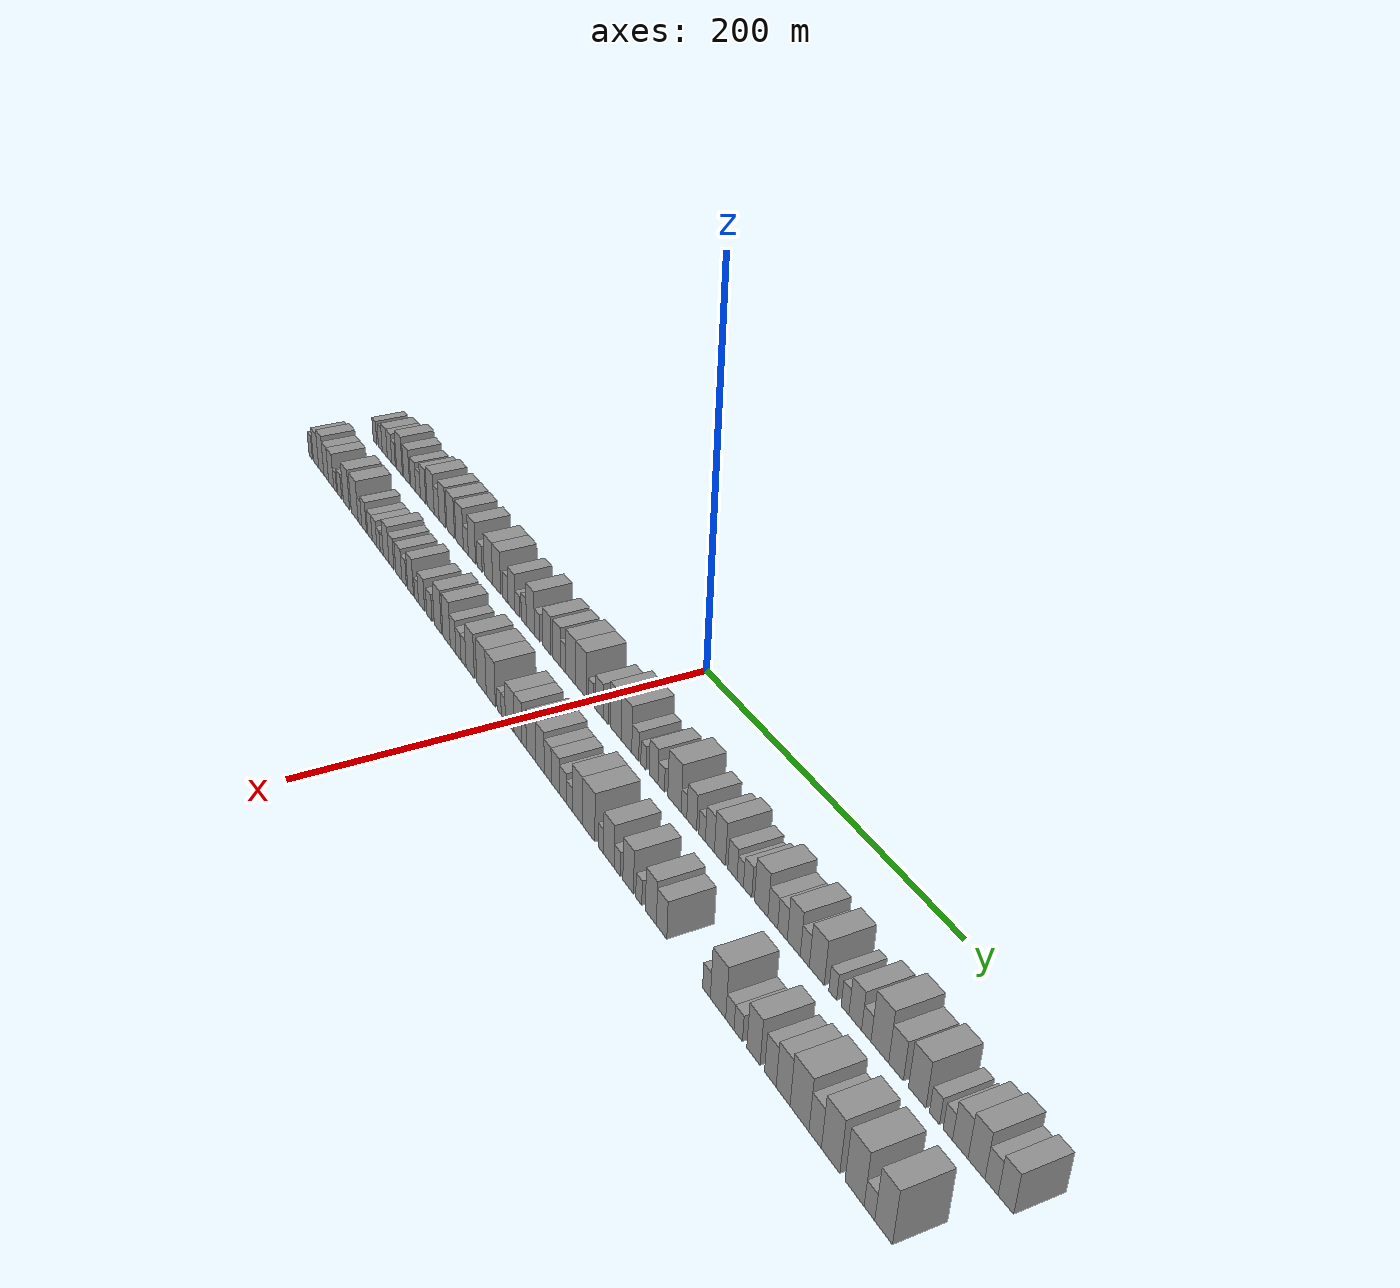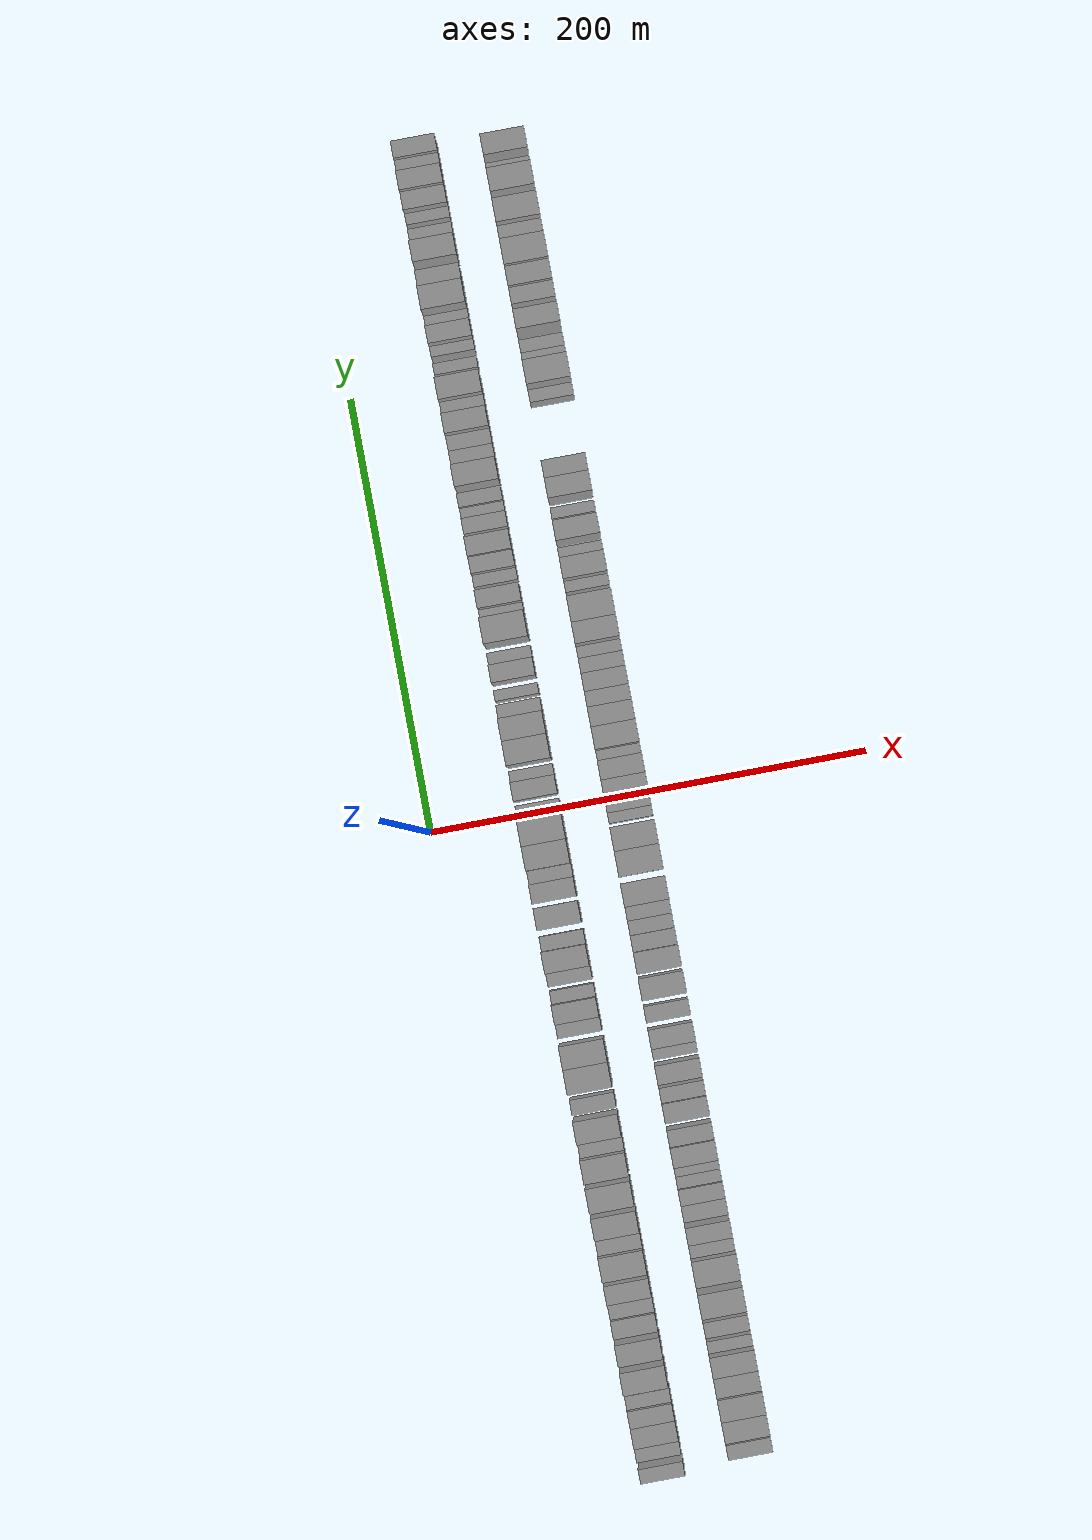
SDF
<sdf version="1.6">
 <world name="default">
  <scene>
   <sky><clouds><speed>12</speed></clouds></sky>
   <ambient>0.4 0.4 0.4 1</ambient>
   <background>0.7 0.7 0.7 1</background>
   <shadows>1</shadows>
  </scene>
  <gravity>0 0 -9.8066</gravity>
  <magnetic_field>6e-06 2.3e-05 -4.2e-05</magnetic_field>
  <physics default="0" name="default_physics" type="ode">
   <ode>
    <solver>
     <type>quick</type>
     <iters>10</iters>
     <sor>1.0</sor>
     <use_dynamic_moi_rescaling>0</use_dynamic_moi_rescaling>
    </solver>
    <constraints>
     <cfm>0</cfm>
     <erp>0.2</erp>
     <contact_max_correcting_vel>100</contact_max_correcting_vel>
     <contact_surface_layer>0.001</contact_surface_layer>
    </constraints>
   </ode>
   <max_step_size>0.004</max_step_size>
   <real_time_factor>1</real_time_factor>
   <real_time_update_rate>250</real_time_update_rate>
  </physics>
  <light name="sun" type="directional">
   <pose>0 0 10 0 0 0</pose>
   <diffuse>0.8 0.8 0.8 1</diffuse>
   <specular>0.2 0.2 0.2 1</specular>
   <attenuation>
    <range>1000</range>
    <constant>0.9</constant>
    <linear>0.01</linear>
    <quadratic>0.001</quadratic>
   </attenuation>
   <direction>-0.5 0.1 -0.9</direction>
  </light>
  <model name="building_1">
   <static>1</static>
   <pose>50.0000 -296.7926 0 0.000000 0.000000 0.000000</pose>
   <link name="link">
    <pose>0 0 7.50 0 0 0</pose>
    <collision name="collision"><geometry><box><size>20.0000 6.4148 15.0000</size></box></geometry></collision>
    <visual name="visual">
     <cast_shadows>0</cast_shadows>
     <geometry><box><size>20.0000 6.4148 15.0000</size></box></geometry>
     <material>
      <script>
       <uri>model://grey_wall/materials/scripts</uri>
       <uri>model://grey_wall/materials/textures</uri>
       <name>vrc/grey_wall</name>
      </script>
     </material>
    </visual>
   </link>
  </model>
  <model name="building_2">
   <static>1</static>
   <pose>50.0000 -287.2635 0 0.000000 0.000000 0.000000</pose>
   <link name="link">
    <pose>0 0 7.50 0 0 0</pose>
    <collision name="collision"><geometry><box><size>20.0000 6.6434 15.0000</size></box></geometry></collision>
    <visual name="visual">
     <cast_shadows>0</cast_shadows>
     <geometry><box><size>20.0000 6.6434 15.0000</size></box></geometry>
     <material>
      <script>
       <uri>model://grey_wall/materials/scripts</uri>
       <uri>model://grey_wall/materials/textures</uri>
       <name>vrc/grey_wall</name>
      </script>
     </material>
    </visual>
   </link>
  </model>
  <model name="building_3">
   <static>1</static>
   <pose>50.0000 -279.4545 0 0.000000 0.000000 0.000000</pose>
   <link name="link">
    <pose>0 0 9.00 0 0 0</pose>
    <collision name="collision"><geometry><box><size>20.0000 8.9747 18.0000</size></box></geometry></collision>
    <visual name="visual">
     <cast_shadows>0</cast_shadows>
     <geometry><box><size>20.0000 8.9747 18.0000</size></box></geometry>
     <material>
      <script>
       <uri>model://grey_wall/materials/scripts</uri>
       <uri>model://grey_wall/materials/textures</uri>
       <name>vrc/grey_wall</name>
      </script>
     </material>
    </visual>
   </link>
  </model>
  <model name="building_4">
   <static>1</static>
   <pose>50.0000 -271.0788 0 0.000000 0.000000 0.000000</pose>
   <link name="link">
    <pose>0 0 9.00 0 0 0</pose>
    <collision name="collision"><geometry><box><size>20.0000 7.7766 18.0000</size></box></geometry></collision>
    <visual name="visual">
     <cast_shadows>0</cast_shadows>
     <geometry><box><size>20.0000 7.7766 18.0000</size></box></geometry>
     <material>
      <script>
       <uri>model://grey_wall/materials/scripts</uri>
       <uri>model://grey_wall/materials/textures</uri>
       <name>vrc/grey_wall</name>
      </script>
     </material>
    </visual>
   </link>
  </model>
  <model name="building_5">
   <static>1</static>
   <pose>50.0000 -264.1244 0 0.000000 0.000000 0.000000</pose>
   <link name="link">
    <pose>0 0 7.50 0 0 0</pose>
    <collision name="collision"><geometry><box><size>20.0000 6.1322 15.0000</size></box></geometry></collision>
    <visual name="visual">
     <cast_shadows>0</cast_shadows>
     <geometry><box><size>20.0000 6.1322 15.0000</size></box></geometry>
     <material>
      <script>
       <uri>model://grey_wall/materials/scripts</uri>
       <uri>model://grey_wall/materials/textures</uri>
       <name>vrc/grey_wall</name>
      </script>
     </material>
    </visual>
   </link>
  </model>
  <model name="building_6">
   <static>1</static>
   <pose>50.0000 -254.0193 0 0.000000 0.000000 0.000000</pose>
   <link name="link">
    <pose>0 0 12.00 0 0 0</pose>
    <collision name="collision"><geometry><box><size>20.0000 10.0782 24.0000</size></box></geometry></collision>
    <visual name="visual">
     <cast_shadows>0</cast_shadows>
     <geometry><box><size>20.0000 10.0782 24.0000</size></box></geometry>
     <material>
      <script>
       <uri>model://grey_wall/materials/scripts</uri>
       <uri>model://grey_wall/materials/textures</uri>
       <name>vrc/grey_wall</name>
      </script>
     </material>
    </visual>
   </link>
  </model>
  <model name="building_7">
   <static>1</static>
   <pose>50.0000 -242.1282 0 0.000000 0.000000 0.000000</pose>
   <link name="link">
    <pose>0 0 10.50 0 0 0</pose>
    <collision name="collision"><geometry><box><size>20.0000 9.7040 21.0000</size></box></geometry></collision>
    <visual name="visual">
     <cast_shadows>0</cast_shadows>
     <geometry><box><size>20.0000 9.7040 21.0000</size></box></geometry>
     <material>
      <script>
       <uri>model://grey_wall/materials/scripts</uri>
       <uri>model://grey_wall/materials/textures</uri>
       <name>vrc/grey_wall</name>
      </script>
     </material>
    </visual>
   </link>
  </model>
  <model name="building_8">
   <static>1</static>
   <pose>50.0000 -231.1623 0 0.000000 0.000000 0.000000</pose>
   <link name="link">
    <pose>0 0 9.00 0 0 0</pose>
    <collision name="collision"><geometry><box><size>20.0000 8.2278 18.0000</size></box></geometry></collision>
    <visual name="visual">
     <cast_shadows>0</cast_shadows>
     <geometry><box><size>20.0000 8.2278 18.0000</size></box></geometry>
     <material>
      <script>
       <uri>model://grey_wall/materials/scripts</uri>
       <uri>model://grey_wall/materials/textures</uri>
       <name>vrc/grey_wall</name>
      </script>
     </material>
    </visual>
   </link>
  </model>
  <model name="building_9">
   <static>1</static>
   <pose>50.0000 -223.3064 0 0.000000 0.000000 0.000000</pose>
   <link name="link">
    <pose>0 0 7.50 0 0 0</pose>
    <collision name="collision"><geometry><box><size>20.0000 7.4841 15.0000</size></box></geometry></collision>
    <visual name="visual">
     <cast_shadows>0</cast_shadows>
     <geometry><box><size>20.0000 7.4841 15.0000</size></box></geometry>
     <material>
      <script>
       <uri>model://grey_wall/materials/scripts</uri>
       <uri>model://grey_wall/materials/textures</uri>
       <name>vrc/grey_wall</name>
      </script>
     </material>
    </visual>
   </link>
  </model>
  <model name="building_10">
   <static>1</static>
   <pose>50.0000 -215.2852 0 0.000000 0.000000 0.000000</pose>
   <link name="link">
    <pose>0 0 10.50 0 0 0</pose>
    <collision name="collision"><geometry><box><size>20.0000 8.5582 21.0000</size></box></geometry></collision>
    <visual name="visual">
     <cast_shadows>0</cast_shadows>
     <geometry><box><size>20.0000 8.5582 21.0000</size></box></geometry>
     <material>
      <script>
       <uri>model://grey_wall/materials/scripts</uri>
       <uri>model://grey_wall/materials/textures</uri>
       <name>vrc/grey_wall</name>
      </script>
     </material>
    </visual>
   </link>
  </model>
  <model name="building_11">
   <static>1</static>
   <pose>50.0000 -203.5275 0 0.000000 0.000000 0.000000</pose>
   <link name="link">
    <pose>0 0 12.00 0 0 0</pose>
    <collision name="collision"><geometry><box><size>20.0000 10.9573 24.0000</size></box></geometry></collision>
    <visual name="visual">
     <cast_shadows>0</cast_shadows>
     <geometry><box><size>20.0000 10.9573 24.0000</size></box></geometry>
     <material>
      <script>
       <uri>model://grey_wall/materials/scripts</uri>
       <uri>model://grey_wall/materials/textures</uri>
       <name>vrc/grey_wall</name>
      </script>
     </material>
    </visual>
   </link>
  </model>
  <model name="building_12">
   <static>1</static>
   <pose>50.0000 -194.2931 0 0.000000 0.000000 0.000000</pose>
   <link name="link">
    <pose>0 0 9.00 0 0 0</pose>
    <collision name="collision"><geometry><box><size>20.0000 7.5116 18.0000</size></box></geometry></collision>
    <visual name="visual">
     <cast_shadows>0</cast_shadows>
     <geometry><box><size>20.0000 7.5116 18.0000</size></box></geometry>
     <material>
      <script>
       <uri>model://grey_wall/materials/scripts</uri>
       <uri>model://grey_wall/materials/textures</uri>
       <name>vrc/grey_wall</name>
      </script>
     </material>
    </visual>
   </link>
  </model>
  <model name="building_13">
   <static>1</static>
   <pose>50.0000 -185.5815 0 0.000000 0.000000 0.000000</pose>
   <link name="link">
    <pose>0 0 12.00 0 0 0</pose>
    <collision name="collision"><geometry><box><size>20.0000 9.9117 24.0000</size></box></geometry></collision>
    <visual name="visual">
     <cast_shadows>0</cast_shadows>
     <geometry><box><size>20.0000 9.9117 24.0000</size></box></geometry>
     <material>
      <script>
       <uri>model://grey_wall/materials/scripts</uri>
       <uri>model://grey_wall/materials/textures</uri>
       <name>vrc/grey_wall</name>
      </script>
     </material>
    </visual>
   </link>
  </model>
  <model name="building_14">
   <static>1</static>
   <pose>50.0000 -173.0200 0 0.000000 0.000000 0.000000</pose>
   <link name="link">
    <pose>0 0 12.00 0 0 0</pose>
    <collision name="collision"><geometry><box><size>20.0000 11.2113 24.0000</size></box></geometry></collision>
    <visual name="visual">
     <cast_shadows>0</cast_shadows>
     <geometry><box><size>20.0000 11.2113 24.0000</size></box></geometry>
     <material>
      <script>
       <uri>model://grey_wall/materials/scripts</uri>
       <uri>model://grey_wall/materials/textures</uri>
       <name>vrc/grey_wall</name>
      </script>
     </material>
    </visual>
   </link>
  </model>
  <model name="building_15">
   <static>1</static>
   <pose>50.0000 -160.0728 0 0.000000 0.000000 0.000000</pose>
   <link name="link">
    <pose>0 0 12.00 0 0 0</pose>
    <collision name="collision"><geometry><box><size>20.0000 10.6831 24.0000</size></box></geometry></collision>
    <visual name="visual">
     <cast_shadows>0</cast_shadows>
     <geometry><box><size>20.0000 10.6831 24.0000</size></box></geometry>
     <material>
      <script>
       <uri>model://grey_wall/materials/scripts</uri>
       <uri>model://grey_wall/materials/textures</uri>
       <name>vrc/grey_wall</name>
      </script>
     </material>
    </visual>
   </link>
  </model>
  <model name="building_16">
   <static>1</static>
   <pose>50.0000 -151.2729 0 0.000000 0.000000 0.000000</pose>
   <link name="link">
    <pose>0 0 7.50 0 0 0</pose>
    <collision name="collision"><geometry><box><size>20.0000 6.9169 15.0000</size></box></geometry></collision>
    <visual name="visual">
     <cast_shadows>0</cast_shadows>
     <geometry><box><size>20.0000 6.9169 15.0000</size></box></geometry>
     <material>
      <script>
       <uri>model://grey_wall/materials/scripts</uri>
       <uri>model://grey_wall/materials/textures</uri>
       <name>vrc/grey_wall</name>
      </script>
     </material>
    </visual>
   </link>
  </model>
  <model name="building_17">
   <static>1</static>
   <pose>50.0000 -142.6974 0 0.000000 0.000000 0.000000</pose>
   <link name="link">
    <pose>0 0 12.00 0 0 0</pose>
    <collision name="collision"><geometry><box><size>20.0000 10.2342 24.0000</size></box></geometry></collision>
    <visual name="visual">
     <cast_shadows>0</cast_shadows>
     <geometry><box><size>20.0000 10.2342 24.0000</size></box></geometry>
     <material>
      <script>
       <uri>model://grey_wall/materials/scripts</uri>
       <uri>model://grey_wall/materials/textures</uri>
       <name>vrc/grey_wall</name>
      </script>
     </material>
    </visual>
   </link>
  </model>
  <model name="building_18">
   <static>1</static>
   <pose>50.0000 -132.1075 0 0.000000 0.000000 0.000000</pose>
   <link name="link">
    <pose>0 0 7.50 0 0 0</pose>
    <collision name="collision"><geometry><box><size>20.0000 6.9456 15.0000</size></box></geometry></collision>
    <visual name="visual">
     <cast_shadows>0</cast_shadows>
     <geometry><box><size>20.0000 6.9456 15.0000</size></box></geometry>
     <material>
      <script>
       <uri>model://grey_wall/materials/scripts</uri>
       <uri>model://grey_wall/materials/textures</uri>
       <name>vrc/grey_wall</name>
      </script>
     </material>
    </visual>
   </link>
  </model>
  <model name="building_19">
   <static>1</static>
   <pose>50.0000 -120.0522 0 0.000000 0.000000 0.000000</pose>
   <link name="link">
    <pose>0 0 12.00 0 0 0</pose>
    <collision name="collision"><geometry><box><size>20.0000 11.1651 24.0000</size></box></geometry></collision>
    <visual name="visual">
     <cast_shadows>0</cast_shadows>
     <geometry><box><size>20.0000 11.1651 24.0000</size></box></geometry>
     <material>
      <script>
       <uri>model://grey_wall/materials/scripts</uri>
       <uri>model://grey_wall/materials/textures</uri>
       <name>vrc/grey_wall</name>
      </script>
     </material>
    </visual>
   </link>
  </model>
  <model name="building_20">
   <static>1</static>
   <pose>50.0000 -109.2274 0 0.000000 0.000000 0.000000</pose>
   <link name="link">
    <pose>0 0 12.00 0 0 0</pose>
    <collision name="collision"><geometry><box><size>20.0000 10.4845 24.0000</size></box></geometry></collision>
    <visual name="visual">
     <cast_shadows>0</cast_shadows>
     <geometry><box><size>20.0000 10.4845 24.0000</size></box></geometry>
     <material>
      <script>
       <uri>model://grey_wall/materials/scripts</uri>
       <uri>model://grey_wall/materials/textures</uri>
       <name>vrc/grey_wall</name>
      </script>
     </material>
    </visual>
   </link>
  </model>
  <model name="building_21">
   <static>1</static>
   <pose>50.0000 -97.7396 0 0.000000 0.000000 0.000000</pose>
   <link name="link">
    <pose>0 0 7.50 0 0 0</pose>
    <collision name="collision"><geometry><box><size>20.0000 6.4911 15.0000</size></box></geometry></collision>
    <visual name="visual">
     <cast_shadows>0</cast_shadows>
     <geometry><box><size>20.0000 6.4911 15.0000</size></box></geometry>
     <material>
      <script>
       <uri>model://grey_wall/materials/scripts</uri>
       <uri>model://grey_wall/materials/textures</uri>
       <name>vrc/grey_wall</name>
      </script>
     </material>
    </visual>
   </link>
  </model>
  <model name="building_22">
   <static>1</static>
   <pose>50.0000 -90.0830 0 0.000000 0.000000 0.000000</pose>
   <link name="link">
    <pose>0 0 10.50 0 0 0</pose>
    <collision name="collision"><geometry><box><size>20.0000 8.8221 21.0000</size></box></geometry></collision>
    <visual name="visual">
     <cast_shadows>0</cast_shadows>
     <geometry><box><size>20.0000 8.8221 21.0000</size></box></geometry>
     <material>
      <script>
       <uri>model://grey_wall/materials/scripts</uri>
       <uri>model://grey_wall/materials/textures</uri>
       <name>vrc/grey_wall</name>
      </script>
     </material>
    </visual>
   </link>
  </model>
  <model name="building_23">
   <static>1</static>
   <pose>50.0000 -82.6973 0 0.000000 0.000000 0.000000</pose>
   <link name="link">
    <pose>0 0 6.00 0 0 0</pose>
    <collision name="collision"><geometry><box><size>20.0000 5.9494 12.0000</size></box></geometry></collision>
    <visual name="visual">
     <cast_shadows>0</cast_shadows>
     <geometry><box><size>20.0000 5.9494 12.0000</size></box></geometry>
     <material>
      <script>
       <uri>model://grey_wall/materials/scripts</uri>
       <uri>model://grey_wall/materials/textures</uri>
       <name>vrc/grey_wall</name>
      </script>
     </material>
    </visual>
   </link>
  </model>
  <model name="building_24">
   <static>1</static>
   <pose>50.0000 -74.6171 0 0.000000 0.000000 0.000000</pose>
   <link name="link">
    <pose>0 0 7.50 0 0 0</pose>
    <collision name="collision"><geometry><box><size>20.0000 6.2110 15.0000</size></box></geometry></collision>
    <visual name="visual">
     <cast_shadows>0</cast_shadows>
     <geometry><box><size>20.0000 6.2110 15.0000</size></box></geometry>
     <material>
      <script>
       <uri>model://grey_wall/materials/scripts</uri>
       <uri>model://grey_wall/materials/textures</uri>
       <name>vrc/grey_wall</name>
      </script>
     </material>
    </visual>
   </link>
  </model>
  <model name="building_25">
   <static>1</static>
   <pose>50.0000 -66.6309 0 0.000000 0.000000 0.000000</pose>
   <link name="link">
    <pose>0 0 12.00 0 0 0</pose>
    <collision name="collision"><geometry><box><size>20.0000 9.7614 24.0000</size></box></geometry></collision>
    <visual name="visual">
     <cast_shadows>0</cast_shadows>
     <geometry><box><size>20.0000 9.7614 24.0000</size></box></geometry>
     <material>
      <script>
       <uri>model://grey_wall/materials/scripts</uri>
       <uri>model://grey_wall/materials/textures</uri>
       <name>vrc/grey_wall</name>
      </script>
     </material>
    </visual>
   </link>
  </model>
  <model name="building_26">
   <static>1</static>
   <pose>50.0000 -58.4410 0 0.000000 0.000000 0.000000</pose>
   <link name="link">
    <pose>0 0 7.50 0 0 0</pose>
    <collision name="collision"><geometry><box><size>20.0000 6.6184 15.0000</size></box></geometry></collision>
    <visual name="visual">
     <cast_shadows>0</cast_shadows>
     <geometry><box><size>20.0000 6.6184 15.0000</size></box></geometry>
     <material>
      <script>
       <uri>model://grey_wall/materials/scripts</uri>
       <uri>model://grey_wall/materials/textures</uri>
       <name>vrc/grey_wall</name>
      </script>
     </material>
    </visual>
   </link>
  </model>
  <model name="building_27">
   <static>1</static>
   <pose>50.0000 -47.1898 0 0.000000 0.000000 0.000000</pose>
   <link name="link">
    <pose>0 0 10.50 0 0 0</pose>
    <collision name="collision"><geometry><box><size>20.0000 9.8840 21.0000</size></box></geometry></collision>
    <visual name="visual">
     <cast_shadows>0</cast_shadows>
     <geometry><box><size>20.0000 9.8840 21.0000</size></box></geometry>
     <material>
      <script>
       <uri>model://grey_wall/materials/scripts</uri>
       <uri>model://grey_wall/materials/textures</uri>
       <name>vrc/grey_wall</name>
      </script>
     </material>
    </visual>
   </link>
  </model>
  <model name="building_28">
   <static>1</static>
   <pose>50.0000 -35.8952 0 0.000000 0.000000 0.000000</pose>
   <link name="link">
    <pose>0 0 10.50 0 0 0</pose>
    <collision name="collision"><geometry><box><size>20.0000 8.7052 21.0000</size></box></geometry></collision>
    <visual name="visual">
     <cast_shadows>0</cast_shadows>
     <geometry><box><size>20.0000 8.7052 21.0000</size></box></geometry>
     <material>
      <script>
       <uri>model://grey_wall/materials/scripts</uri>
       <uri>model://grey_wall/materials/textures</uri>
       <name>vrc/grey_wall</name>
      </script>
     </material>
    </visual>
   </link>
  </model>
  <model name="building_29">
   <static>1</static>
   <pose>50.0000 -28.4702 0 0.000000 0.000000 0.000000</pose>
   <link name="link">
    <pose>0 0 7.50 0 0 0</pose>
    <collision name="collision"><geometry><box><size>20.0000 6.1448 15.0000</size></box></geometry></collision>
    <visual name="visual">
     <cast_shadows>0</cast_shadows>
     <geometry><box><size>20.0000 6.1448 15.0000</size></box></geometry>
     <material>
      <script>
       <uri>model://grey_wall/materials/scripts</uri>
       <uri>model://grey_wall/materials/textures</uri>
       <name>vrc/grey_wall</name>
      </script>
     </material>
    </visual>
   </link>
  </model>
  <model name="building_30">
   <static>1</static>
   <pose>50.0000 -19.9293 0 0.000000 0.000000 0.000000</pose>
   <link name="link">
    <pose>0 0 12.00 0 0 0</pose>
    <collision name="collision"><geometry><box><size>20.0000 10.9371 24.0000</size></box></geometry></collision>
    <visual name="visual">
     <cast_shadows>0</cast_shadows>
     <geometry><box><size>20.0000 10.9371 24.0000</size></box></geometry>
     <material>
      <script>
       <uri>model://grey_wall/materials/scripts</uri>
       <uri>model://grey_wall/materials/textures</uri>
       <name>vrc/grey_wall</name>
      </script>
     </material>
    </visual>
   </link>
  </model>
  <model name="building_31">
   <static>1</static>
   <pose>50.0000 -8.8116 0 0.000000 0.000000 0.000000</pose>
   <link name="link">
    <pose>0 0 12.00 0 0 0</pose>
    <collision name="collision"><geometry><box><size>20.0000 11.2982 24.0000</size></box></geometry></collision>
    <visual name="visual">
     <cast_shadows>0</cast_shadows>
     <geometry><box><size>20.0000 11.2982 24.0000</size></box></geometry>
     <material>
      <script>
       <uri>model://grey_wall/materials/scripts</uri>
       <uri>model://grey_wall/materials/textures</uri>
       <name>vrc/grey_wall</name>
      </script>
     </material>
    </visual>
   </link>
  </model>
  <model name="building_32">
   <static>1</static>
   <pose>50.0000 1.5083 0 0.000000 0.000000 0.000000</pose>
   <link name="link">
    <pose>0 0 6.00 0 0 0</pose>
    <collision name="collision"><geometry><box><size>20.0000 5.3416 12.0000</size></box></geometry></collision>
    <visual name="visual">
     <cast_shadows>0</cast_shadows>
     <geometry><box><size>20.0000 5.3416 12.0000</size></box></geometry>
     <material>
      <script>
       <uri>model://grey_wall/materials/scripts</uri>
       <uri>model://grey_wall/materials/textures</uri>
       <name>vrc/grey_wall</name>
      </script>
     </material>
    </visual>
   </link>
  </model>
  <model name="building_33">
   <static>1</static>
   <pose>50.0000 10.4126 0 0.000000 0.000000 0.000000</pose>
   <link name="link">
    <pose>0 0 9.00 0 0 0</pose>
    <collision name="collision"><geometry><box><size>20.0000 8.4670 18.0000</size></box></geometry></collision>
    <visual name="visual">
     <cast_shadows>0</cast_shadows>
     <geometry><box><size>20.0000 8.4670 18.0000</size></box></geometry>
     <material>
      <script>
       <uri>model://grey_wall/materials/scripts</uri>
       <uri>model://grey_wall/materials/textures</uri>
       <name>vrc/grey_wall</name>
      </script>
     </material>
    </visual>
   </link>
  </model>
  <model name="building_34">
   <static>1</static>
   <pose>50.0000 17.2850 0 0.000000 0.000000 0.000000</pose>
   <link name="link">
    <pose>0 0 6.00 0 0 0</pose>
    <collision name="collision"><geometry><box><size>20.0000 5.2779 12.0000</size></box></geometry></collision>
    <visual name="visual">
     <cast_shadows>0</cast_shadows>
     <geometry><box><size>20.0000 5.2779 12.0000</size></box></geometry>
     <material>
      <script>
       <uri>model://grey_wall/materials/scripts</uri>
       <uri>model://grey_wall/materials/textures</uri>
       <name>vrc/grey_wall</name>
      </script>
     </material>
    </visual>
   </link>
  </model>
  <model name="building_35">
   <static>1</static>
   <pose>50.0000 27.4227 0 0.000000 0.000000 0.000000</pose>
   <link name="link">
    <pose>0 0 12.00 0 0 0</pose>
    <collision name="collision"><geometry><box><size>20.0000 10.9975 24.0000</size></box></geometry></collision>
    <visual name="visual">
     <cast_shadows>0</cast_shadows>
     <geometry><box><size>20.0000 10.9975 24.0000</size></box></geometry>
     <material>
      <script>
       <uri>model://grey_wall/materials/scripts</uri>
       <uri>model://grey_wall/materials/textures</uri>
       <name>vrc/grey_wall</name>
      </script>
     </material>
    </visual>
   </link>
  </model>
  <model name="building_36">
   <static>1</static>
   <pose>50.0000 38.0736 0 0.000000 0.000000 0.000000</pose>
   <link name="link">
    <pose>0 0 12.00 0 0 0</pose>
    <collision name="collision"><geometry><box><size>20.0000 10.3042 24.0000</size></box></geometry></collision>
    <visual name="visual">
     <cast_shadows>0</cast_shadows>
     <geometry><box><size>20.0000 10.3042 24.0000</size></box></geometry>
     <material>
      <script>
       <uri>model://grey_wall/materials/scripts</uri>
       <uri>model://grey_wall/materials/textures</uri>
       <name>vrc/grey_wall</name>
      </script>
     </material>
    </visual>
   </link>
  </model>
  <model name="building_37">
   <static>1</static>
   <pose>50.0000 46.5629 0 0.000000 0.000000 0.000000</pose>
   <link name="link">
    <pose>0 0 7.50 0 0 0</pose>
    <collision name="collision"><geometry><box><size>20.0000 6.6744 15.0000</size></box></geometry></collision>
    <visual name="visual">
     <cast_shadows>0</cast_shadows>
     <geometry><box><size>20.0000 6.6744 15.0000</size></box></geometry>
     <material>
      <script>
       <uri>model://grey_wall/materials/scripts</uri>
       <uri>model://grey_wall/materials/textures</uri>
       <name>vrc/grey_wall</name>
      </script>
     </material>
    </visual>
   </link>
  </model>
  <model name="building_38">
   <static>1</static>
   <pose>50.0000 54.3566 0 0.000000 0.000000 0.000000</pose>
   <link name="link">
    <pose>0 0 6.00 0 0 0</pose>
    <collision name="collision"><geometry><box><size>20.0000 4.9131 12.0000</size></box></geometry></collision>
    <visual name="visual">
     <cast_shadows>0</cast_shadows>
     <geometry><box><size>20.0000 4.9131 12.0000</size></box></geometry>
     <material>
      <script>
       <uri>model://grey_wall/materials/scripts</uri>
       <uri>model://grey_wall/materials/textures</uri>
       <name>vrc/grey_wall</name>
      </script>
     </material>
    </visual>
   </link>
  </model>
  <model name="building_39">
   <static>1</static>
   <pose>50.0000 63.8687 0 0.000000 0.000000 0.000000</pose>
   <link name="link">
    <pose>0 0 9.00 0 0 0</pose>
    <collision name="collision"><geometry><box><size>20.0000 8.1110 18.0000</size></box></geometry></collision>
    <visual name="visual">
     <cast_shadows>0</cast_shadows>
     <geometry><box><size>20.0000 8.1110 18.0000</size></box></geometry>
     <material>
      <script>
       <uri>model://grey_wall/materials/scripts</uri>
       <uri>model://grey_wall/materials/textures</uri>
       <name>vrc/grey_wall</name>
      </script>
     </material>
    </visual>
   </link>
  </model>
  <model name="building_40">
   <static>1</static>
   <pose>50.0000 70.8743 0 0.000000 0.000000 0.000000</pose>
   <link name="link">
    <pose>0 0 6.00 0 0 0</pose>
    <collision name="collision"><geometry><box><size>20.0000 5.9002 12.0000</size></box></geometry></collision>
    <visual name="visual">
     <cast_shadows>0</cast_shadows>
     <geometry><box><size>20.0000 5.9002 12.0000</size></box></geometry>
     <material>
      <script>
       <uri>model://grey_wall/materials/scripts</uri>
       <uri>model://grey_wall/materials/textures</uri>
       <name>vrc/grey_wall</name>
      </script>
     </material>
    </visual>
   </link>
  </model>
  <model name="building_41">
   <static>1</static>
   <pose>50.0000 82.7837 0 0.000000 0.000000 0.000000</pose>
   <link name="link">
    <pose>0 0 12.00 0 0 0</pose>
    <collision name="collision"><geometry><box><size>20.0000 11.9186 24.0000</size></box></geometry></collision>
    <visual name="visual">
     <cast_shadows>0</cast_shadows>
     <geometry><box><size>20.0000 11.9186 24.0000</size></box></geometry>
     <material>
      <script>
       <uri>model://grey_wall/materials/scripts</uri>
       <uri>model://grey_wall/materials/textures</uri>
       <name>vrc/grey_wall</name>
      </script>
     </material>
    </visual>
   </link>
  </model>
  <model name="building_42">
   <static>1</static>
   <pose>50.0000 91.1797 0 0.000000 0.000000 0.000000</pose>
   <link name="link">
    <pose>0 0 6.00 0 0 0</pose>
    <collision name="collision"><geometry><box><size>20.0000 4.8735 12.0000</size></box></geometry></collision>
    <visual name="visual">
     <cast_shadows>0</cast_shadows>
     <geometry><box><size>20.0000 4.8735 12.0000</size></box></geometry>
     <material>
      <script>
       <uri>model://grey_wall/materials/scripts</uri>
       <uri>model://grey_wall/materials/textures</uri>
       <name>vrc/grey_wall</name>
      </script>
     </material>
    </visual>
   </link>
  </model>
  <model name="building_43">
   <static>1</static>
   <pose>50.0000 97.7854 0 0.000000 0.000000 0.000000</pose>
   <link name="link">
    <pose>0 0 9.00 0 0 0</pose>
    <collision name="collision"><geometry><box><size>20.0000 8.3379 18.0000</size></box></geometry></collision>
    <visual name="visual">
     <cast_shadows>0</cast_shadows>
     <geometry><box><size>20.0000 8.3379 18.0000</size></box></geometry>
     <material>
      <script>
       <uri>model://grey_wall/materials/scripts</uri>
       <uri>model://grey_wall/materials/textures</uri>
       <name>vrc/grey_wall</name>
      </script>
     </material>
    </visual>
   </link>
  </model>
  <model name="building_44">
   <static>1</static>
   <pose>50.0000 106.7046 0 0.000000 0.000000 0.000000</pose>
   <link name="link">
    <pose>0 0 6.00 0 0 0</pose>
    <collision name="collision"><geometry><box><size>20.0000 5.5005 12.0000</size></box></geometry></collision>
    <visual name="visual">
     <cast_shadows>0</cast_shadows>
     <geometry><box><size>20.0000 5.5005 12.0000</size></box></geometry>
     <material>
      <script>
       <uri>model://grey_wall/materials/scripts</uri>
       <uri>model://grey_wall/materials/textures</uri>
       <name>vrc/grey_wall</name>
      </script>
     </material>
    </visual>
   </link>
  </model>
  <model name="building_45">
   <static>1</static>
   <pose>50.0000 113.2035 0 0.000000 0.000000 0.000000</pose>
   <link name="link">
    <pose>0 0 9.00 0 0 0</pose>
    <collision name="collision"><geometry><box><size>20.0000 7.4973 18.0000</size></box></geometry></collision>
    <visual name="visual">
     <cast_shadows>0</cast_shadows>
     <geometry><box><size>20.0000 7.4973 18.0000</size></box></geometry>
     <material>
      <script>
       <uri>model://grey_wall/materials/scripts</uri>
       <uri>model://grey_wall/materials/textures</uri>
       <name>vrc/grey_wall</name>
      </script>
     </material>
    </visual>
   </link>
  </model>
  <model name="building_46">
   <static>1</static>
   <pose>50.0000 121.3791 0 0.000000 0.000000 0.000000</pose>
   <link name="link">
    <pose>0 0 10.50 0 0 0</pose>
    <collision name="collision"><geometry><box><size>20.0000 8.8538 21.0000</size></box></geometry></collision>
    <visual name="visual">
     <cast_shadows>0</cast_shadows>
     <geometry><box><size>20.0000 8.8538 21.0000</size></box></geometry>
     <material>
      <script>
       <uri>model://grey_wall/materials/scripts</uri>
       <uri>model://grey_wall/materials/textures</uri>
       <name>vrc/grey_wall</name>
      </script>
     </material>
    </visual>
   </link>
  </model>
  <model name="building_47">
   <static>1</static>
   <pose>50.0000 131.4339 0 0.000000 0.000000 0.000000</pose>
   <link name="link">
    <pose>0 0 7.50 0 0 0</pose>
    <collision name="collision"><geometry><box><size>20.0000 7.2557 15.0000</size></box></geometry></collision>
    <visual name="visual">
     <cast_shadows>0</cast_shadows>
     <geometry><box><size>20.0000 7.2557 15.0000</size></box></geometry>
     <material>
      <script>
       <uri>model://grey_wall/materials/scripts</uri>
       <uri>model://grey_wall/materials/textures</uri>
       <name>vrc/grey_wall</name>
      </script>
     </material>
    </visual>
   </link>
  </model>
  <model name="building_48">
   <static>1</static>
   <pose>50.0000 137.5498 0 0.000000 0.000000 0.000000</pose>
   <link name="link">
    <pose>0 0 6.00 0 0 0</pose>
    <collision name="collision"><geometry><box><size>20.0000 4.9761 12.0000</size></box></geometry></collision>
    <visual name="visual">
     <cast_shadows>0</cast_shadows>
     <geometry><box><size>20.0000 4.9761 12.0000</size></box></geometry>
     <material>
      <script>
       <uri>model://grey_wall/materials/scripts</uri>
       <uri>model://grey_wall/materials/textures</uri>
       <name>vrc/grey_wall</name>
      </script>
     </material>
    </visual>
   </link>
  </model>
  <model name="building_49">
   <static>1</static>
   <pose>50.0000 143.2701 0 0.000000 0.000000 0.000000</pose>
   <link name="link">
    <pose>0 0 7.50 0 0 0</pose>
    <collision name="collision"><geometry><box><size>20.0000 6.4646 15.0000</size></box></geometry></collision>
    <visual name="visual">
     <cast_shadows>0</cast_shadows>
     <geometry><box><size>20.0000 6.4646 15.0000</size></box></geometry>
     <material>
      <script>
       <uri>model://grey_wall/materials/scripts</uri>
       <uri>model://grey_wall/materials/textures</uri>
       <name>vrc/grey_wall</name>
      </script>
     </material>
    </visual>
   </link>
  </model>
  <model name="building_50">
   <static>1</static>
   <pose>50.0000 153.5760 0 0.000000 0.000000 0.000000</pose>
   <link name="link">
    <pose>0 0 10.50 0 0 0</pose>
    <collision name="collision"><geometry><box><size>20.0000 10.1470 21.0000</size></box></geometry></collision>
    <visual name="visual">
     <cast_shadows>0</cast_shadows>
     <geometry><box><size>20.0000 10.1470 21.0000</size></box></geometry>
     <material>
      <script>
       <uri>model://grey_wall/materials/scripts</uri>
       <uri>model://grey_wall/materials/textures</uri>
       <name>vrc/grey_wall</name>
      </script>
     </material>
    </visual>
   </link>
  </model>
  <model name="building_51">
   <static>1</static>
   <pose>50.0000 162.2512 0 0.000000 0.000000 0.000000</pose>
   <link name="link">
    <pose>0 0 7.50 0 0 0</pose>
    <collision name="collision"><geometry><box><size>20.0000 7.2035 15.0000</size></box></geometry></collision>
    <visual name="visual">
     <cast_shadows>0</cast_shadows>
     <geometry><box><size>20.0000 7.2035 15.0000</size></box></geometry>
     <material>
      <script>
       <uri>model://grey_wall/materials/scripts</uri>
       <uri>model://grey_wall/materials/textures</uri>
       <name>vrc/grey_wall</name>
      </script>
     </material>
    </visual>
   </link>
  </model>
  <model name="building_52">
   <static>1</static>
   <pose>50.0000 169.3217 0 0.000000 0.000000 0.000000</pose>
   <link name="link">
    <pose>0 0 7.50 0 0 0</pose>
    <collision name="collision"><geometry><box><size>20.0000 6.9376 15.0000</size></box></geometry></collision>
    <visual name="visual">
     <cast_shadows>0</cast_shadows>
     <geometry><box><size>20.0000 6.9376 15.0000</size></box></geometry>
     <material>
      <script>
       <uri>model://grey_wall/materials/scripts</uri>
       <uri>model://grey_wall/materials/textures</uri>
       <name>vrc/grey_wall</name>
      </script>
     </material>
    </visual>
   </link>
  </model>
  <model name="building_53">
   <static>1</static>
   <pose>50.0000 177.3946 0 0.000000 0.000000 0.000000</pose>
   <link name="link">
    <pose>0 0 10.50 0 0 0</pose>
    <collision name="collision"><geometry><box><size>20.0000 9.2082 21.0000</size></box></geometry></collision>
    <visual name="visual">
     <cast_shadows>0</cast_shadows>
     <geometry><box><size>20.0000 9.2082 21.0000</size></box></geometry>
     <material>
      <script>
       <uri>model://grey_wall/materials/scripts</uri>
       <uri>model://grey_wall/materials/textures</uri>
       <name>vrc/grey_wall</name>
      </script>
     </material>
    </visual>
   </link>
  </model>
  <model name="building_54">
   <static>1</static>
   <pose>50.0000 185.1473 0 0.000000 0.000000 0.000000</pose>
   <link name="link">
    <pose>0 0 7.50 0 0 0</pose>
    <collision name="collision"><geometry><box><size>20.0000 6.2972 15.0000</size></box></geometry></collision>
    <visual name="visual">
     <cast_shadows>0</cast_shadows>
     <geometry><box><size>20.0000 6.2972 15.0000</size></box></geometry>
     <material>
      <script>
       <uri>model://grey_wall/materials/scripts</uri>
       <uri>model://grey_wall/materials/textures</uri>
       <name>vrc/grey_wall</name>
      </script>
     </material>
    </visual>
   </link>
  </model>
  <model name="building_55">
   <static>1</static>
   <pose>50.0000 193.3929 0 0.000000 0.000000 0.000000</pose>
   <link name="link">
    <pose>0 0 10.50 0 0 0</pose>
    <collision name="collision"><geometry><box><size>20.0000 10.1941 21.0000</size></box></geometry></collision>
    <visual name="visual">
     <cast_shadows>0</cast_shadows>
     <geometry><box><size>20.0000 10.1941 21.0000</size></box></geometry>
     <material>
      <script>
       <uri>model://grey_wall/materials/scripts</uri>
       <uri>model://grey_wall/materials/textures</uri>
       <name>vrc/grey_wall</name>
      </script>
     </material>
    </visual>
   </link>
  </model>
  <model name="building_56">
   <static>1</static>
   <pose>50.0000 204.0819 0 0.000000 0.000000 0.000000</pose>
   <link name="link">
    <pose>0 0 6.00 0 0 0</pose>
    <collision name="collision"><geometry><box><size>20.0000 5.1838 12.0000</size></box></geometry></collision>
    <visual name="visual">
     <cast_shadows>0</cast_shadows>
     <geometry><box><size>20.0000 5.1838 12.0000</size></box></geometry>
     <material>
      <script>
       <uri>model://grey_wall/materials/scripts</uri>
       <uri>model://grey_wall/materials/textures</uri>
       <name>vrc/grey_wall</name>
      </script>
     </material>
    </visual>
   </link>
  </model>
  <model name="building_57">
   <static>1</static>
   <pose>50.0000 212.1471 0 0.000000 0.000000 0.000000</pose>
   <link name="link">
    <pose>0 0 6.00 0 0 0</pose>
    <collision name="collision"><geometry><box><size>20.0000 4.9467 12.0000</size></box></geometry></collision>
    <visual name="visual">
     <cast_shadows>0</cast_shadows>
     <geometry><box><size>20.0000 4.9467 12.0000</size></box></geometry>
     <material>
      <script>
       <uri>model://grey_wall/materials/scripts</uri>
       <uri>model://grey_wall/materials/textures</uri>
       <name>vrc/grey_wall</name>
      </script>
     </material>
    </visual>
   </link>
  </model>
  <model name="building_58">
   <static>1</static>
   <pose>50.0000 218.6658 0 0.000000 0.000000 0.000000</pose>
   <link name="link">
    <pose>0 0 9.00 0 0 0</pose>
    <collision name="collision"><geometry><box><size>20.0000 8.0906 18.0000</size></box></geometry></collision>
    <visual name="visual">
     <cast_shadows>0</cast_shadows>
     <geometry><box><size>20.0000 8.0906 18.0000</size></box></geometry>
     <material>
      <script>
       <uri>model://grey_wall/materials/scripts</uri>
       <uri>model://grey_wall/materials/textures</uri>
       <name>vrc/grey_wall</name>
      </script>
     </material>
    </visual>
   </link>
  </model>
  <model name="building_59">
   <static>1</static>
   <pose>50.0000 225.6367 0 0.000000 0.000000 0.000000</pose>
   <link name="link">
    <pose>0 0 6.00 0 0 0</pose>
    <collision name="collision"><geometry><box><size>20.0000 5.8513 12.0000</size></box></geometry></collision>
    <visual name="visual">
     <cast_shadows>0</cast_shadows>
     <geometry><box><size>20.0000 5.8513 12.0000</size></box></geometry>
     <material>
      <script>
       <uri>model://grey_wall/materials/scripts</uri>
       <uri>model://grey_wall/materials/textures</uri>
       <name>vrc/grey_wall</name>
      </script>
     </material>
    </visual>
   </link>
  </model>
  <model name="building_60">
   <static>1</static>
   <pose>50.0000 233.9612 0 0.000000 0.000000 0.000000</pose>
   <link name="link">
    <pose>0 0 12.00 0 0 0</pose>
    <collision name="collision"><geometry><box><size>20.0000 10.7978 24.0000</size></box></geometry></collision>
    <visual name="visual">
     <cast_shadows>0</cast_shadows>
     <geometry><box><size>20.0000 10.7978 24.0000</size></box></geometry>
     <material>
      <script>
       <uri>model://grey_wall/materials/scripts</uri>
       <uri>model://grey_wall/materials/textures</uri>
       <name>vrc/grey_wall</name>
      </script>
     </material>
    </visual>
   </link>
  </model>
  <model name="building_61">
   <static>1</static>
   <pose>50.0000 243.7472 0 0.000000 0.000000 0.000000</pose>
   <link name="link">
    <pose>0 0 9.00 0 0 0</pose>
    <collision name="collision"><geometry><box><size>20.0000 8.7741 18.0000</size></box></geometry></collision>
    <visual name="visual">
     <cast_shadows>0</cast_shadows>
     <geometry><box><size>20.0000 8.7741 18.0000</size></box></geometry>
     <material>
      <script>
       <uri>model://grey_wall/materials/scripts</uri>
       <uri>model://grey_wall/materials/textures</uri>
       <name>vrc/grey_wall</name>
      </script>
     </material>
    </visual>
   </link>
  </model>
  <model name="building_62">
   <static>1</static>
   <pose>50.0000 256.1199 0 0.000000 0.000000 0.000000</pose>
   <link name="link">
    <pose>0 0 10.50 0 0 0</pose>
    <collision name="collision"><geometry><box><size>20.0000 9.9713 21.0000</size></box></geometry></collision>
    <visual name="visual">
     <cast_shadows>0</cast_shadows>
     <geometry><box><size>20.0000 9.9713 21.0000</size></box></geometry>
     <material>
      <script>
       <uri>model://grey_wall/materials/scripts</uri>
       <uri>model://grey_wall/materials/textures</uri>
       <name>vrc/grey_wall</name>
      </script>
     </material>
    </visual>
   </link>
  </model>
  <model name="building_63">
   <static>1</static>
   <pose>50.0000 265.9240 0 0.000000 0.000000 0.000000</pose>
   <link name="link">
    <pose>0 0 6.00 0 0 0</pose>
    <collision name="collision"><geometry><box><size>20.0000 5.6369 12.0000</size></box></geometry></collision>
    <visual name="visual">
     <cast_shadows>0</cast_shadows>
     <geometry><box><size>20.0000 5.6369 12.0000</size></box></geometry>
     <material>
      <script>
       <uri>model://grey_wall/materials/scripts</uri>
       <uri>model://grey_wall/materials/textures</uri>
       <name>vrc/grey_wall</name>
      </script>
     </material>
    </visual>
   </link>
  </model>
  <model name="building_64">
   <static>1</static>
   <pose>50.0000 273.3273 0 0.000000 0.000000 0.000000</pose>
   <link name="link">
    <pose>0 0 6.00 0 0 0</pose>
    <collision name="collision"><geometry><box><size>20.0000 5.1697 12.0000</size></box></geometry></collision>
    <visual name="visual">
     <cast_shadows>0</cast_shadows>
     <geometry><box><size>20.0000 5.1697 12.0000</size></box></geometry>
     <material>
      <script>
       <uri>model://grey_wall/materials/scripts</uri>
       <uri>model://grey_wall/materials/textures</uri>
       <name>vrc/grey_wall</name>
      </script>
     </material>
    </visual>
   </link>
  </model>
  <model name="building_65">
   <static>1</static>
   <pose>50.0000 280.0449 0 0.000000 0.000000 0.000000</pose>
   <link name="link">
    <pose>0 0 9.00 0 0 0</pose>
    <collision name="collision"><geometry><box><size>20.0000 8.2655 18.0000</size></box></geometry></collision>
    <visual name="visual">
     <cast_shadows>0</cast_shadows>
     <geometry><box><size>20.0000 8.2655 18.0000</size></box></geometry>
     <material>
      <script>
       <uri>model://grey_wall/materials/scripts</uri>
       <uri>model://grey_wall/materials/textures</uri>
       <name>vrc/grey_wall</name>
      </script>
     </material>
    </visual>
   </link>
  </model>
  <model name="building_66">
   <static>1</static>
   <pose>50.0000 288.5966 0 0.000000 0.000000 0.000000</pose>
   <link name="link">
    <pose>0 0 10.50 0 0 0</pose>
    <collision name="collision"><geometry><box><size>20.0000 8.8379 21.0000</size></box></geometry></collision>
    <visual name="visual">
     <cast_shadows>0</cast_shadows>
     <geometry><box><size>20.0000 8.8379 21.0000</size></box></geometry>
     <material>
      <script>
       <uri>model://grey_wall/materials/scripts</uri>
       <uri>model://grey_wall/materials/textures</uri>
       <name>vrc/grey_wall</name>
      </script>
     </material>
    </visual>
   </link>
  </model>
  <model name="building_67">
   <static>1</static>
   <pose>50.0000 296.3832 0 0.000000 0.000000 0.000000</pose>
   <link name="link">
    <pose>0 0 7.50 0 0 0</pose>
    <collision name="collision"><geometry><box><size>20.0000 6.7354 15.0000</size></box></geometry></collision>
    <visual name="visual">
     <cast_shadows>0</cast_shadows>
     <geometry><box><size>20.0000 6.7354 15.0000</size></box></geometry>
     <material>
      <script>
       <uri>model://grey_wall/materials/scripts</uri>
       <uri>model://grey_wall/materials/textures</uri>
       <name>vrc/grey_wall</name>
      </script>
     </material>
    </visual>
   </link>
  </model>
  <model name="building_68">
   <static>1</static>
   <pose>50.0000 303.6786 0 0.000000 0.000000 0.000000</pose>
   <link name="link">
    <pose>0 0 9.00 0 0 0</pose>
    <collision name="collision"><geometry><box><size>20.0000 7.8553 18.0000</size></box></geometry></collision>
    <visual name="visual">
     <cast_shadows>0</cast_shadows>
     <geometry><box><size>20.0000 7.8553 18.0000</size></box></geometry>
     <material>
      <script>
       <uri>model://grey_wall/materials/scripts</uri>
       <uri>model://grey_wall/materials/textures</uri>
       <name>vrc/grey_wall</name>
      </script>
     </material>
    </visual>
   </link>
  </model>
  <model name="building_69">
   <static>1</static>
   <pose>90.0000 -293.6930 0 0.000000 0.000000 0.000000</pose>
   <link name="link">
    <pose>0 0 7.50 0 0 0</pose>
    <collision name="collision"><geometry><box><size>20.0000 6.6141 15.0000</size></box></geometry></collision>
    <visual name="visual">
     <cast_shadows>0</cast_shadows>
     <geometry><box><size>20.0000 6.6141 15.0000</size></box></geometry>
     <material>
      <script>
       <uri>model://grey_wall/materials/scripts</uri>
       <uri>model://grey_wall/materials/textures</uri>
       <name>vrc/grey_wall</name>
      </script>
     </material>
    </visual>
   </link>
  </model>
  <model name="building_70">
   <static>1</static>
   <pose>90.0000 -283.3321 0 0.000000 0.000000 0.000000</pose>
   <link name="link">
    <pose>0 0 10.50 0 0 0</pose>
    <collision name="collision"><geometry><box><size>20.0000 10.1076 21.0000</size></box></geometry></collision>
    <visual name="visual">
     <cast_shadows>0</cast_shadows>
     <geometry><box><size>20.0000 10.1076 21.0000</size></box></geometry>
     <material>
      <script>
       <uri>model://grey_wall/materials/scripts</uri>
       <uri>model://grey_wall/materials/textures</uri>
       <name>vrc/grey_wall</name>
      </script>
     </material>
    </visual>
   </link>
  </model>
  <model name="building_71">
   <static>1</static>
   <pose>90.0000 -273.3265 0 0.000000 0.000000 0.000000</pose>
   <link name="link">
    <pose>0 0 12.00 0 0 0</pose>
    <collision name="collision"><geometry><box><size>20.0000 9.9035 24.0000</size></box></geometry></collision>
    <visual name="visual">
     <cast_shadows>0</cast_shadows>
     <geometry><box><size>20.0000 9.9035 24.0000</size></box></geometry>
     <material>
      <script>
       <uri>model://grey_wall/materials/scripts</uri>
       <uri>model://grey_wall/materials/textures</uri>
       <name>vrc/grey_wall</name>
      </script>
     </material>
    </visual>
   </link>
  </model>
  <model name="building_72">
   <static>1</static>
   <pose>90.0000 -264.0152 0 0.000000 0.000000 0.000000</pose>
   <link name="link">
    <pose>0 0 10.50 0 0 0</pose>
    <collision name="collision"><geometry><box><size>20.0000 8.7190 21.0000</size></box></geometry></collision>
    <visual name="visual">
     <cast_shadows>0</cast_shadows>
     <geometry><box><size>20.0000 8.7190 21.0000</size></box></geometry>
     <material>
      <script>
       <uri>model://grey_wall/materials/scripts</uri>
       <uri>model://grey_wall/materials/textures</uri>
       <name>vrc/grey_wall</name>
      </script>
     </material>
    </visual>
   </link>
  </model>
  <model name="building_73">
   <static>1</static>
   <pose>90.0000 -254.9657 0 0.000000 0.000000 0.000000</pose>
   <link name="link">
    <pose>0 0 10.50 0 0 0</pose>
    <collision name="collision"><geometry><box><size>20.0000 9.3799 21.0000</size></box></geometry></collision>
    <visual name="visual">
     <cast_shadows>0</cast_shadows>
     <geometry><box><size>20.0000 9.3799 21.0000</size></box></geometry>
     <material>
      <script>
       <uri>model://grey_wall/materials/scripts</uri>
       <uri>model://grey_wall/materials/textures</uri>
       <name>vrc/grey_wall</name>
      </script>
     </material>
    </visual>
   </link>
  </model>
  <model name="building_74">
   <static>1</static>
   <pose>90.0000 -247.5824 0 0.000000 0.000000 0.000000</pose>
   <link name="link">
    <pose>0 0 6.00 0 0 0</pose>
    <collision name="collision"><geometry><box><size>20.0000 5.3867 12.0000</size></box></geometry></collision>
    <visual name="visual">
     <cast_shadows>0</cast_shadows>
     <geometry><box><size>20.0000 5.3867 12.0000</size></box></geometry>
     <material>
      <script>
       <uri>model://grey_wall/materials/scripts</uri>
       <uri>model://grey_wall/materials/textures</uri>
       <name>vrc/grey_wall</name>
      </script>
     </material>
    </visual>
   </link>
  </model>
  <model name="building_75">
   <static>1</static>
   <pose>90.0000 -239.3895 0 0.000000 0.000000 0.000000</pose>
   <link name="link">
    <pose>0 0 7.50 0 0 0</pose>
    <collision name="collision"><geometry><box><size>20.0000 6.9991 15.0000</size></box></geometry></collision>
    <visual name="visual">
     <cast_shadows>0</cast_shadows>
     <geometry><box><size>20.0000 6.9991 15.0000</size></box></geometry>
     <material>
      <script>
       <uri>model://grey_wall/materials/scripts</uri>
       <uri>model://grey_wall/materials/textures</uri>
       <name>vrc/grey_wall</name>
      </script>
     </material>
    </visual>
   </link>
  </model>
  <model name="building_76">
   <static>1</static>
   <pose>90.0000 -227.4014 0 0.000000 0.000000 0.000000</pose>
   <link name="link">
    <pose>0 0 12.00 0 0 0</pose>
    <collision name="collision"><geometry><box><size>20.0000 10.9771 24.0000</size></box></geometry></collision>
    <visual name="visual">
     <cast_shadows>0</cast_shadows>
     <geometry><box><size>20.0000 10.9771 24.0000</size></box></geometry>
     <material>
      <script>
       <uri>model://grey_wall/materials/scripts</uri>
       <uri>model://grey_wall/materials/textures</uri>
       <name>vrc/grey_wall</name>
      </script>
     </material>
    </visual>
   </link>
  </model>
  <model name="building_77">
   <static>1</static>
   <pose>90.0000 -213.0505 0 0.000000 0.000000 0.000000</pose>
   <link name="link">
    <pose>0 0 12.00 0 0 0</pose>
    <collision name="collision"><geometry><box><size>20.0000 11.7247 24.0000</size></box></geometry></collision>
    <visual name="visual">
     <cast_shadows>0</cast_shadows>
     <geometry><box><size>20.0000 11.7247 24.0000</size></box></geometry>
     <material>
      <script>
       <uri>model://grey_wall/materials/scripts</uri>
       <uri>model://grey_wall/materials/textures</uri>
       <name>vrc/grey_wall</name>
      </script>
     </material>
    </visual>
   </link>
  </model>
  <model name="building_78">
   <static>1</static>
   <pose>90.0000 -204.1069 0 0.000000 0.000000 0.000000</pose>
   <link name="link">
    <pose>0 0 7.50 0 0 0</pose>
    <collision name="collision"><geometry><box><size>20.0000 6.1624 15.0000</size></box></geometry></collision>
    <visual name="visual">
     <cast_shadows>0</cast_shadows>
     <geometry><box><size>20.0000 6.1624 15.0000</size></box></geometry>
     <material>
      <script>
       <uri>model://grey_wall/materials/scripts</uri>
       <uri>model://grey_wall/materials/textures</uri>
       <name>vrc/grey_wall</name>
      </script>
     </material>
    </visual>
   </link>
  </model>
  <model name="building_79">
   <static>1</static>
   <pose>90.0000 -197.0779 0 0.000000 0.000000 0.000000</pose>
   <link name="link">
    <pose>0 0 9.00 0 0 0</pose>
    <collision name="collision"><geometry><box><size>20.0000 7.8958 18.0000</size></box></geometry></collision>
    <visual name="visual">
     <cast_shadows>0</cast_shadows>
     <geometry><box><size>20.0000 7.8958 18.0000</size></box></geometry>
     <material>
      <script>
       <uri>model://grey_wall/materials/scripts</uri>
       <uri>model://grey_wall/materials/textures</uri>
       <name>vrc/grey_wall</name>
      </script>
     </material>
    </visual>
   </link>
  </model>
  <model name="building_80">
   <static>1</static>
   <pose>90.0000 -187.4497 0 0.000000 0.000000 0.000000</pose>
   <link name="link">
    <pose>0 0 7.50 0 0 0</pose>
    <collision name="collision"><geometry><box><size>20.0000 7.3606 15.0000</size></box></geometry></collision>
    <visual name="visual">
     <cast_shadows>0</cast_shadows>
     <geometry><box><size>20.0000 7.3606 15.0000</size></box></geometry>
     <material>
      <script>
       <uri>model://grey_wall/materials/scripts</uri>
       <uri>model://grey_wall/materials/textures</uri>
       <name>vrc/grey_wall</name>
      </script>
     </material>
    </visual>
   </link>
  </model>
  <model name="building_81">
   <static>1</static>
   <pose>90.0000 -180.1134 0 0.000000 0.000000 0.000000</pose>
   <link name="link">
    <pose>0 0 7.50 0 0 0</pose>
    <collision name="collision"><geometry><box><size>20.0000 7.3119 15.0000</size></box></geometry></collision>
    <visual name="visual">
     <cast_shadows>0</cast_shadows>
     <geometry><box><size>20.0000 7.3119 15.0000</size></box></geometry>
     <material>
      <script>
       <uri>model://grey_wall/materials/scripts</uri>
       <uri>model://grey_wall/materials/textures</uri>
       <name>vrc/grey_wall</name>
      </script>
     </material>
    </visual>
   </link>
  </model>
  <model name="building_82">
   <static>1</static>
   <pose>90.0000 -173.7316 0 0.000000 0.000000 0.000000</pose>
   <link name="link">
    <pose>0 0 6.00 0 0 0</pose>
    <collision name="collision"><geometry><box><size>20.0000 5.4518 12.0000</size></box></geometry></collision>
    <visual name="visual">
     <cast_shadows>0</cast_shadows>
     <geometry><box><size>20.0000 5.4518 12.0000</size></box></geometry>
     <material>
      <script>
       <uri>model://grey_wall/materials/scripts</uri>
       <uri>model://grey_wall/materials/textures</uri>
       <name>vrc/grey_wall</name>
      </script>
     </material>
    </visual>
   </link>
  </model>
  <model name="building_83">
   <static>1</static>
   <pose>90.0000 -168.5272 0 0.000000 0.000000 0.000000</pose>
   <link name="link">
    <pose>0 0 6.00 0 0 0</pose>
    <collision name="collision"><geometry><box><size>20.0000 4.9570 12.0000</size></box></geometry></collision>
    <visual name="visual">
     <cast_shadows>0</cast_shadows>
     <geometry><box><size>20.0000 4.9570 12.0000</size></box></geometry>
     <material>
      <script>
       <uri>model://grey_wall/materials/scripts</uri>
       <uri>model://grey_wall/materials/textures</uri>
       <name>vrc/grey_wall</name>
      </script>
     </material>
    </visual>
   </link>
  </model>
  <model name="building_84">
   <static>1</static>
   <pose>90.0000 -161.5450 0 0.000000 0.000000 0.000000</pose>
   <link name="link">
    <pose>0 0 10.50 0 0 0</pose>
    <collision name="collision"><geometry><box><size>20.0000 9.0074 21.0000</size></box></geometry></collision>
    <visual name="visual">
     <cast_shadows>0</cast_shadows>
     <geometry><box><size>20.0000 9.0074 21.0000</size></box></geometry>
     <material>
      <script>
       <uri>model://grey_wall/materials/scripts</uri>
       <uri>model://grey_wall/materials/textures</uri>
       <name>vrc/grey_wall</name>
      </script>
     </material>
    </visual>
   </link>
  </model>
  <model name="building_85">
   <static>1</static>
   <pose>90.0000 -153.2507 0 0.000000 0.000000 0.000000</pose>
   <link name="link">
    <pose>0 0 9.00 0 0 0</pose>
    <collision name="collision"><geometry><box><size>20.0000 7.5812 18.0000</size></box></geometry></collision>
    <visual name="visual">
     <cast_shadows>0</cast_shadows>
     <geometry><box><size>20.0000 7.5812 18.0000</size></box></geometry>
     <material>
      <script>
       <uri>model://grey_wall/materials/scripts</uri>
       <uri>model://grey_wall/materials/textures</uri>
       <name>vrc/grey_wall</name>
      </script>
     </material>
    </visual>
   </link>
  </model>
  <model name="building_86">
   <static>1</static>
   <pose>90.0000 -142.0244 0 0.000000 0.000000 0.000000</pose>
   <link name="link">
    <pose>0 0 9.00 0 0 0</pose>
    <collision name="collision"><geometry><box><size>20.0000 8.8716 18.0000</size></box></geometry></collision>
    <visual name="visual">
     <cast_shadows>0</cast_shadows>
     <geometry><box><size>20.0000 8.8716 18.0000</size></box></geometry>
     <material>
      <script>
       <uri>model://grey_wall/materials/scripts</uri>
       <uri>model://grey_wall/materials/textures</uri>
       <name>vrc/grey_wall</name>
      </script>
     </material>
    </visual>
   </link>
  </model>
  <model name="building_87">
   <static>1</static>
   <pose>90.0000 -134.1826 0 0.000000 0.000000 0.000000</pose>
   <link name="link">
    <pose>0 0 7.50 0 0 0</pose>
    <collision name="collision"><geometry><box><size>20.0000 6.8118 15.0000</size></box></geometry></collision>
    <visual name="visual">
     <cast_shadows>0</cast_shadows>
     <geometry><box><size>20.0000 6.8118 15.0000</size></box></geometry>
     <material>
      <script>
       <uri>model://grey_wall/materials/scripts</uri>
       <uri>model://grey_wall/materials/textures</uri>
       <name>vrc/grey_wall</name>
      </script>
     </material>
    </visual>
   </link>
  </model>
  <model name="building_88">
   <static>1</static>
   <pose>90.0000 -124.5405 0 0.000000 0.000000 0.000000</pose>
   <link name="link">
    <pose>0 0 10.50 0 0 0</pose>
    <collision name="collision"><geometry><box><size>20.0000 8.4725 21.0000</size></box></geometry></collision>
    <visual name="visual">
     <cast_shadows>0</cast_shadows>
     <geometry><box><size>20.0000 8.4725 21.0000</size></box></geometry>
     <material>
      <script>
       <uri>model://grey_wall/materials/scripts</uri>
       <uri>model://grey_wall/materials/textures</uri>
       <name>vrc/grey_wall</name>
      </script>
     </material>
    </visual>
   </link>
  </model>
  <model name="building_89">
   <static>1</static>
   <pose>90.0000 -115.7239 0 0.000000 0.000000 0.000000</pose>
   <link name="link">
    <pose>0 0 6.00 0 0 0</pose>
    <collision name="collision"><geometry><box><size>20.0000 5.1607 12.0000</size></box></geometry></collision>
    <visual name="visual">
     <cast_shadows>0</cast_shadows>
     <geometry><box><size>20.0000 5.1607 12.0000</size></box></geometry>
     <material>
      <script>
       <uri>model://grey_wall/materials/scripts</uri>
       <uri>model://grey_wall/materials/textures</uri>
       <name>vrc/grey_wall</name>
      </script>
     </material>
    </visual>
   </link>
  </model>
  <model name="building_90">
   <static>1</static>
   <pose>90.0000 -108.7787 0 0.000000 0.000000 0.000000</pose>
   <link name="link">
    <pose>0 0 9.00 0 0 0</pose>
    <collision name="collision"><geometry><box><size>20.0000 8.7297 18.0000</size></box></geometry></collision>
    <visual name="visual">
     <cast_shadows>0</cast_shadows>
     <geometry><box><size>20.0000 8.7297 18.0000</size></box></geometry>
     <material>
      <script>
       <uri>model://grey_wall/materials/scripts</uri>
       <uri>model://grey_wall/materials/textures</uri>
       <name>vrc/grey_wall</name>
      </script>
     </material>
    </visual>
   </link>
  </model>
  <model name="building_91">
   <static>1</static>
   <pose>90.0000 -97.7153 0 0.000000 0.000000 0.000000</pose>
   <link name="link">
    <pose>0 0 7.50 0 0 0</pose>
    <collision name="collision"><geometry><box><size>20.0000 7.3970 15.0000</size></box></geometry></collision>
    <visual name="visual">
     <cast_shadows>0</cast_shadows>
     <geometry><box><size>20.0000 7.3970 15.0000</size></box></geometry>
     <material>
      <script>
       <uri>model://grey_wall/materials/scripts</uri>
       <uri>model://grey_wall/materials/textures</uri>
       <name>vrc/grey_wall</name>
      </script>
     </material>
    </visual>
   </link>
  </model>
  <model name="building_92">
   <static>1</static>
   <pose>90.0000 -86.0694 0 0.000000 0.000000 0.000000</pose>
   <link name="link">
    <pose>0 0 12.00 0 0 0</pose>
    <collision name="collision"><geometry><box><size>20.0000 9.8949 24.0000</size></box></geometry></collision>
    <visual name="visual">
     <cast_shadows>0</cast_shadows>
     <geometry><box><size>20.0000 9.8949 24.0000</size></box></geometry>
     <material>
      <script>
       <uri>model://grey_wall/materials/scripts</uri>
       <uri>model://grey_wall/materials/textures</uri>
       <name>vrc/grey_wall</name>
      </script>
     </material>
    </visual>
   </link>
  </model>
  <model name="building_93">
   <static>1</static>
   <pose>90.0000 -74.2831 0 0.000000 0.000000 0.000000</pose>
   <link name="link">
    <pose>0 0 12.00 0 0 0</pose>
    <collision name="collision"><geometry><box><size>20.0000 9.6777 24.0000</size></box></geometry></collision>
    <visual name="visual">
     <cast_shadows>0</cast_shadows>
     <geometry><box><size>20.0000 9.6777 24.0000</size></box></geometry>
     <material>
      <script>
       <uri>model://grey_wall/materials/scripts</uri>
       <uri>model://grey_wall/materials/textures</uri>
       <name>vrc/grey_wall</name>
      </script>
     </material>
    </visual>
   </link>
  </model>
  <model name="building_94">
   <static>1</static>
   <pose>90.0000 -65.7197 0 0.000000 0.000000 0.000000</pose>
   <link name="link">
    <pose>0 0 9.00 0 0 0</pose>
    <collision name="collision"><geometry><box><size>20.0000 7.4491 18.0000</size></box></geometry></collision>
    <visual name="visual">
     <cast_shadows>0</cast_shadows>
     <geometry><box><size>20.0000 7.4491 18.0000</size></box></geometry>
     <material>
      <script>
       <uri>model://grey_wall/materials/scripts</uri>
       <uri>model://grey_wall/materials/textures</uri>
       <name>vrc/grey_wall</name>
      </script>
     </material>
    </visual>
   </link>
  </model>
  <model name="building_95">
   <static>1</static>
   <pose>90.0000 -58.7277 0 0.000000 0.000000 0.000000</pose>
   <link name="link">
    <pose>0 0 7.50 0 0 0</pose>
    <collision name="collision"><geometry><box><size>20.0000 6.5348 15.0000</size></box></geometry></collision>
    <visual name="visual">
     <cast_shadows>0</cast_shadows>
     <geometry><box><size>20.0000 6.5348 15.0000</size></box></geometry>
     <material>
      <script>
       <uri>model://grey_wall/materials/scripts</uri>
       <uri>model://grey_wall/materials/textures</uri>
       <name>vrc/grey_wall</name>
      </script>
     </material>
    </visual>
   </link>
  </model>
  <model name="building_96">
   <static>1</static>
   <pose>90.0000 -52.2620 0 0.000000 0.000000 0.000000</pose>
   <link name="link">
    <pose>0 0 7.50 0 0 0</pose>
    <collision name="collision"><geometry><box><size>20.0000 6.3967 15.0000</size></box></geometry></collision>
    <visual name="visual">
     <cast_shadows>0</cast_shadows>
     <geometry><box><size>20.0000 6.3967 15.0000</size></box></geometry>
     <material>
      <script>
       <uri>model://grey_wall/materials/scripts</uri>
       <uri>model://grey_wall/materials/textures</uri>
       <name>vrc/grey_wall</name>
      </script>
     </material>
    </visual>
   </link>
  </model>
  <model name="building_97">
   <static>1</static>
   <pose>90.0000 -43.8292 0 0.000000 0.000000 0.000000</pose>
   <link name="link">
    <pose>0 0 12.00 0 0 0</pose>
    <collision name="collision"><geometry><box><size>20.0000 10.4689 24.0000</size></box></geometry></collision>
    <visual name="visual">
     <cast_shadows>0</cast_shadows>
     <geometry><box><size>20.0000 10.4689 24.0000</size></box></geometry>
     <material>
      <script>
       <uri>model://grey_wall/materials/scripts</uri>
       <uri>model://grey_wall/materials/textures</uri>
       <name>vrc/grey_wall</name>
      </script>
     </material>
    </visual>
   </link>
  </model>
  <model name="building_98">
   <static>1</static>
   <pose>90.0000 -29.8407 0 0.000000 0.000000 0.000000</pose>
   <link name="link">
    <pose>0 0 12.00 0 0 0</pose>
    <collision name="collision"><geometry><box><size>20.0000 11.5080 24.0000</size></box></geometry></collision>
    <visual name="visual">
     <cast_shadows>0</cast_shadows>
     <geometry><box><size>20.0000 11.5080 24.0000</size></box></geometry>
     <material>
      <script>
       <uri>model://grey_wall/materials/scripts</uri>
       <uri>model://grey_wall/materials/textures</uri>
       <name>vrc/grey_wall</name>
      </script>
     </material>
    </visual>
   </link>
  </model>
  <model name="building_99">
   <static>1</static>
   <pose>90.0000 -18.6864 0 0.000000 0.000000 0.000000</pose>
   <link name="link">
    <pose>0 0 12.00 0 0 0</pose>
    <collision name="collision"><geometry><box><size>20.0000 10.8007 24.0000</size></box></geometry></collision>
    <visual name="visual">
     <cast_shadows>0</cast_shadows>
     <geometry><box><size>20.0000 10.8007 24.0000</size></box></geometry>
     <material>
      <script>
       <uri>model://grey_wall/materials/scripts</uri>
       <uri>model://grey_wall/materials/textures</uri>
       <name>vrc/grey_wall</name>
      </script>
     </material>
    </visual>
   </link>
  </model>
  <model name="building_100">
   <static>1</static>
   <pose>90.0000 -8.8683 0 0.000000 0.000000 0.000000</pose>
   <link name="link">
    <pose>0 0 6.00 0 0 0</pose>
    <collision name="collision"><geometry><box><size>20.0000 4.8355 12.0000</size></box></geometry></collision>
    <visual name="visual">
     <cast_shadows>0</cast_shadows>
     <geometry><box><size>20.0000 4.8355 12.0000</size></box></geometry>
     <material>
      <script>
       <uri>model://grey_wall/materials/scripts</uri>
       <uri>model://grey_wall/materials/textures</uri>
       <name>vrc/grey_wall</name>
      </script>
     </material>
    </visual>
   </link>
  </model>
  <model name="building_101">
   <static>1</static>
   <pose>90.0000 -4.0435 0 0.000000 0.000000 0.000000</pose>
   <link name="link">
    <pose>0 0 6.00 0 0 0</pose>
    <collision name="collision"><geometry><box><size>20.0000 4.8141 12.0000</size></box></geometry></collision>
    <visual name="visual">
     <cast_shadows>0</cast_shadows>
     <geometry><box><size>20.0000 4.8141 12.0000</size></box></geometry>
     <material>
      <script>
       <uri>model://grey_wall/materials/scripts</uri>
       <uri>model://grey_wall/materials/textures</uri>
       <name>vrc/grey_wall</name>
      </script>
     </material>
    </visual>
   </link>
  </model>
  <model name="building_102">
   <static>1</static>
   <pose>90.0000 3.2635 0 0.000000 0.000000 0.000000</pose>
   <link name="link">
    <pose>0 0 10.50 0 0 0</pose>
    <collision name="collision"><geometry><box><size>20.0000 9.7999 21.0000</size></box></geometry></collision>
    <visual name="visual">
     <cast_shadows>0</cast_shadows>
     <geometry><box><size>20.0000 9.7999 21.0000</size></box></geometry>
     <material>
      <script>
       <uri>model://grey_wall/materials/scripts</uri>
       <uri>model://grey_wall/materials/textures</uri>
       <name>vrc/grey_wall</name>
      </script>
     </material>
    </visual>
   </link>
  </model>
  <model name="building_103">
   <static>1</static>
   <pose>90.0000 12.5319 0 0.000000 0.000000 0.000000</pose>
   <link name="link">
    <pose>0 0 10.50 0 0 0</pose>
    <collision name="collision"><geometry><box><size>20.0000 8.7368 21.0000</size></box></geometry></collision>
    <visual name="visual">
     <cast_shadows>0</cast_shadows>
     <geometry><box><size>20.0000 8.7368 21.0000</size></box></geometry>
     <material>
      <script>
       <uri>model://grey_wall/materials/scripts</uri>
       <uri>model://grey_wall/materials/textures</uri>
       <name>vrc/grey_wall</name>
      </script>
     </material>
    </visual>
   </link>
  </model>
  <model name="building_104">
   <static>1</static>
   <pose>90.0000 19.4082 0 0.000000 0.000000 0.000000</pose>
   <link name="link">
    <pose>0 0 6.00 0 0 0</pose>
    <collision name="collision"><geometry><box><size>20.0000 5.0158 12.0000</size></box></geometry></collision>
    <visual name="visual">
     <cast_shadows>0</cast_shadows>
     <geometry><box><size>20.0000 5.0158 12.0000</size></box></geometry>
     <material>
      <script>
       <uri>model://grey_wall/materials/scripts</uri>
       <uri>model://grey_wall/materials/textures</uri>
       <name>vrc/grey_wall</name>
      </script>
     </material>
    </visual>
   </link>
  </model>
  <model name="building_105">
   <static>1</static>
   <pose>90.0000 27.0254 0 0.000000 0.000000 0.000000</pose>
   <link name="link">
    <pose>0 0 10.50 0 0 0</pose>
    <collision name="collision"><geometry><box><size>20.0000 10.2185 21.0000</size></box></geometry></collision>
    <visual name="visual">
     <cast_shadows>0</cast_shadows>
     <geometry><box><size>20.0000 10.2185 21.0000</size></box></geometry>
     <material>
      <script>
       <uri>model://grey_wall/materials/scripts</uri>
       <uri>model://grey_wall/materials/textures</uri>
       <name>vrc/grey_wall</name>
      </script>
     </material>
    </visual>
   </link>
  </model>
  <model name="building_106">
   <static>1</static>
   <pose>90.0000 36.6132 0 0.000000 0.000000 0.000000</pose>
   <link name="link">
    <pose>0 0 10.50 0 0 0</pose>
    <collision name="collision"><geometry><box><size>20.0000 8.9573 21.0000</size></box></geometry></collision>
    <visual name="visual">
     <cast_shadows>0</cast_shadows>
     <geometry><box><size>20.0000 8.9573 21.0000</size></box></geometry>
     <material>
      <script>
       <uri>model://grey_wall/materials/scripts</uri>
       <uri>model://grey_wall/materials/textures</uri>
       <name>vrc/grey_wall</name>
      </script>
     </material>
    </visual>
   </link>
  </model>
  <model name="building_107">
   <static>1</static>
   <pose>90.0000 44.7175 0 0.000000 0.000000 0.000000</pose>
   <link name="link">
    <pose>0 0 9.00 0 0 0</pose>
    <collision name="collision"><geometry><box><size>20.0000 7.2513 18.0000</size></box></geometry></collision>
    <visual name="visual">
     <cast_shadows>0</cast_shadows>
     <geometry><box><size>20.0000 7.2513 18.0000</size></box></geometry>
     <material>
      <script>
       <uri>model://grey_wall/materials/scripts</uri>
       <uri>model://grey_wall/materials/textures</uri>
       <name>vrc/grey_wall</name>
      </script>
     </material>
    </visual>
   </link>
  </model>
  <model name="building_108">
   <static>1</static>
   <pose>90.0000 52.5017 0 0.000000 0.000000 0.000000</pose>
   <link name="link">
    <pose>0 0 9.00 0 0 0</pose>
    <collision name="collision"><geometry><box><size>20.0000 8.3170 18.0000</size></box></geometry></collision>
    <visual name="visual">
     <cast_shadows>0</cast_shadows>
     <geometry><box><size>20.0000 8.3170 18.0000</size></box></geometry>
     <material>
      <script>
       <uri>model://grey_wall/materials/scripts</uri>
       <uri>model://grey_wall/materials/textures</uri>
       <name>vrc/grey_wall</name>
      </script>
     </material>
    </visual>
   </link>
  </model>
  <model name="building_109">
   <static>1</static>
   <pose>90.0000 60.1761 0 0.000000 0.000000 0.000000</pose>
   <link name="link">
    <pose>0 0 7.50 0 0 0</pose>
    <collision name="collision"><geometry><box><size>20.0000 7.0318 15.0000</size></box></geometry></collision>
    <visual name="visual">
     <cast_shadows>0</cast_shadows>
     <geometry><box><size>20.0000 7.0318 15.0000</size></box></geometry>
     <material>
      <script>
       <uri>model://grey_wall/materials/scripts</uri>
       <uri>model://grey_wall/materials/textures</uri>
       <name>vrc/grey_wall</name>
      </script>
     </material>
    </visual>
   </link>
  </model>
  <model name="building_110">
   <static>1</static>
   <pose>90.0000 66.5430 0 0.000000 0.000000 0.000000</pose>
   <link name="link">
    <pose>0 0 6.00 0 0 0</pose>
    <collision name="collision"><geometry><box><size>20.0000 5.7021 12.0000</size></box></geometry></collision>
    <visual name="visual">
     <cast_shadows>0</cast_shadows>
     <geometry><box><size>20.0000 5.7021 12.0000</size></box></geometry>
     <material>
      <script>
       <uri>model://grey_wall/materials/scripts</uri>
       <uri>model://grey_wall/materials/textures</uri>
       <name>vrc/grey_wall</name>
      </script>
     </material>
    </visual>
   </link>
  </model>
  <model name="building_111">
   <static>1</static>
   <pose>90.0000 74.2761 0 0.000000 0.000000 0.000000</pose>
   <link name="link">
    <pose>0 0 12.00 0 0 0</pose>
    <collision name="collision"><geometry><box><size>20.0000 9.7640 24.0000</size></box></geometry></collision>
    <visual name="visual">
     <cast_shadows>0</cast_shadows>
     <geometry><box><size>20.0000 9.7640 24.0000</size></box></geometry>
     <material>
      <script>
       <uri>model://grey_wall/materials/scripts</uri>
       <uri>model://grey_wall/materials/textures</uri>
       <name>vrc/grey_wall</name>
      </script>
     </material>
    </visual>
   </link>
  </model>
  <model name="building_112">
   <static>1</static>
   <pose>90.0000 85.1190 0 0.000000 0.000000 0.000000</pose>
   <link name="link">
    <pose>0 0 12.00 0 0 0</pose>
    <collision name="collision"><geometry><box><size>20.0000 11.9219 24.0000</size></box></geometry></collision>
    <visual name="visual">
     <cast_shadows>0</cast_shadows>
     <geometry><box><size>20.0000 11.9219 24.0000</size></box></geometry>
     <material>
      <script>
       <uri>model://grey_wall/materials/scripts</uri>
       <uri>model://grey_wall/materials/textures</uri>
       <name>vrc/grey_wall</name>
      </script>
     </material>
    </visual>
   </link>
  </model>
  <model name="building_113">
   <static>1</static>
   <pose>90.0000 96.6389 0 0.000000 0.000000 0.000000</pose>
   <link name="link">
    <pose>0 0 6.00 0 0 0</pose>
    <collision name="collision"><geometry><box><size>20.0000 5.1179 12.0000</size></box></geometry></collision>
    <visual name="visual">
     <cast_shadows>0</cast_shadows>
     <geometry><box><size>20.0000 5.1179 12.0000</size></box></geometry>
     <material>
      <script>
       <uri>model://grey_wall/materials/scripts</uri>
       <uri>model://grey_wall/materials/textures</uri>
       <name>vrc/grey_wall</name>
      </script>
     </material>
    </visual>
   </link>
  </model>
  <model name="building_114">
   <static>1</static>
   <pose>90.0000 104.0124 0 0.000000 0.000000 0.000000</pose>
   <link name="link">
    <pose>0 0 10.50 0 0 0</pose>
    <collision name="collision"><geometry><box><size>20.0000 9.6290 21.0000</size></box></geometry></collision>
    <visual name="visual">
     <cast_shadows>0</cast_shadows>
     <geometry><box><size>20.0000 9.6290 21.0000</size></box></geometry>
     <material>
      <script>
       <uri>model://grey_wall/materials/scripts</uri>
       <uri>model://grey_wall/materials/textures</uri>
       <name>vrc/grey_wall</name>
      </script>
     </material>
    </visual>
   </link>
  </model>
  <model name="building_115">
   <static>1</static>
   <pose>90.0000 111.6711 0 0.000000 0.000000 0.000000</pose>
   <link name="link">
    <pose>0 0 6.00 0 0 0</pose>
    <collision name="collision"><geometry><box><size>20.0000 5.6885 12.0000</size></box></geometry></collision>
    <visual name="visual">
     <cast_shadows>0</cast_shadows>
     <geometry><box><size>20.0000 5.6885 12.0000</size></box></geometry>
     <material>
      <script>
       <uri>model://grey_wall/materials/scripts</uri>
       <uri>model://grey_wall/materials/textures</uri>
       <name>vrc/grey_wall</name>
      </script>
     </material>
    </visual>
   </link>
  </model>
  <model name="building_116">
   <static>1</static>
   <pose>90.0000 121.1224 0 0.000000 0.000000 0.000000</pose>
   <link name="link">
    <pose>0 0 10.50 0 0 0</pose>
    <collision name="collision"><geometry><box><size>20.0000 9.2140 21.0000</size></box></geometry></collision>
    <visual name="visual">
     <cast_shadows>0</cast_shadows>
     <geometry><box><size>20.0000 9.2140 21.0000</size></box></geometry>
     <material>
      <script>
       <uri>model://grey_wall/materials/scripts</uri>
       <uri>model://grey_wall/materials/textures</uri>
       <name>vrc/grey_wall</name>
      </script>
     </material>
    </visual>
   </link>
  </model>
  <model name="building_117">
   <static>1</static>
   <pose>90.0000 130.2792 0 0.000000 0.000000 0.000000</pose>
   <link name="link">
    <pose>0 0 6.00 0 0 0</pose>
    <collision name="collision"><geometry><box><size>20.0000 5.0997 12.0000</size></box></geometry></collision>
    <visual name="visual">
     <cast_shadows>0</cast_shadows>
     <geometry><box><size>20.0000 5.0997 12.0000</size></box></geometry>
     <material>
      <script>
       <uri>model://grey_wall/materials/scripts</uri>
       <uri>model://grey_wall/materials/textures</uri>
       <name>vrc/grey_wall</name>
      </script>
     </material>
    </visual>
   </link>
  </model>
  <model name="building_118">
   <static>1</static>
   <pose>90.0000 140.4212 0 0.000000 0.000000 0.000000</pose>
   <link name="link">
    <pose>0 0 10.50 0 0 0</pose>
    <collision name="collision"><geometry><box><size>20.0000 9.1842 21.0000</size></box></geometry></collision>
    <visual name="visual">
     <cast_shadows>0</cast_shadows>
     <geometry><box><size>20.0000 9.1842 21.0000</size></box></geometry>
     <material>
      <script>
       <uri>model://grey_wall/materials/scripts</uri>
       <uri>model://grey_wall/materials/textures</uri>
       <name>vrc/grey_wall</name>
      </script>
     </material>
    </visual>
   </link>
  </model>
  <model name="building_119">
   <static>1</static>
   <pose>90.0000 149.2653 0 0.000000 0.000000 0.000000</pose>
   <link name="link">
    <pose>0 0 9.00 0 0 0</pose>
    <collision name="collision"><geometry><box><size>20.0000 8.5042 18.0000</size></box></geometry></collision>
    <visual name="visual">
     <cast_shadows>0</cast_shadows>
     <geometry><box><size>20.0000 8.5042 18.0000</size></box></geometry>
     <material>
      <script>
       <uri>model://grey_wall/materials/scripts</uri>
       <uri>model://grey_wall/materials/textures</uri>
       <name>vrc/grey_wall</name>
      </script>
     </material>
    </visual>
   </link>
  </model>
  <model name="building_120">
   <static>1</static>
   <pose>90.0000 184.1886 0 0.000000 0.000000 0.000000</pose>
   <link name="link">
    <pose>0 0 6.00 0 0 0</pose>
    <collision name="collision"><geometry><box><size>20.0000 5.7808 12.0000</size></box></geometry></collision>
    <visual name="visual">
     <cast_shadows>0</cast_shadows>
     <geometry><box><size>20.0000 5.7808 12.0000</size></box></geometry>
     <material>
      <script>
       <uri>model://grey_wall/materials/scripts</uri>
       <uri>model://grey_wall/materials/textures</uri>
       <name>vrc/grey_wall</name>
      </script>
     </material>
    </visual>
   </link>
  </model>
  <model name="building_121">
   <static>1</static>
   <pose>90.0000 192.6528 0 0.000000 0.000000 0.000000</pose>
   <link name="link">
    <pose>0 0 12.00 0 0 0</pose>
    <collision name="collision"><geometry><box><size>20.0000 11.1475 24.0000</size></box></geometry></collision>
    <visual name="visual">
     <cast_shadows>0</cast_shadows>
     <geometry><box><size>20.0000 11.1475 24.0000</size></box></geometry>
     <material>
      <script>
       <uri>model://grey_wall/materials/scripts</uri>
       <uri>model://grey_wall/materials/textures</uri>
       <name>vrc/grey_wall</name>
      </script>
     </material>
    </visual>
   </link>
  </model>
  <model name="building_122">
   <static>1</static>
   <pose>90.0000 201.1807 0 0.000000 0.000000 0.000000</pose>
   <link name="link">
    <pose>0 0 6.00 0 0 0</pose>
    <collision name="collision"><geometry><box><size>20.0000 5.9083 12.0000</size></box></geometry></collision>
    <visual name="visual">
     <cast_shadows>0</cast_shadows>
     <geometry><box><size>20.0000 5.9083 12.0000</size></box></geometry>
     <material>
      <script>
       <uri>model://grey_wall/materials/scripts</uri>
       <uri>model://grey_wall/materials/textures</uri>
       <name>vrc/grey_wall</name>
      </script>
     </material>
    </visual>
   </link>
  </model>
  <model name="building_123">
   <static>1</static>
   <pose>90.0000 207.0950 0 0.000000 0.000000 0.000000</pose>
   <link name="link">
    <pose>0 0 6.00 0 0 0</pose>
    <collision name="collision"><geometry><box><size>20.0000 5.9203 12.0000</size></box></geometry></collision>
    <visual name="visual">
     <cast_shadows>0</cast_shadows>
     <geometry><box><size>20.0000 5.9203 12.0000</size></box></geometry>
     <material>
      <script>
       <uri>model://grey_wall/materials/scripts</uri>
       <uri>model://grey_wall/materials/textures</uri>
       <name>vrc/grey_wall</name>
      </script>
     </material>
    </visual>
   </link>
  </model>
  <model name="building_124">
   <static>1</static>
   <pose>90.0000 217.5665 0 0.000000 0.000000 0.000000</pose>
   <link name="link">
    <pose>0 0 10.50 0 0 0</pose>
    <collision name="collision"><geometry><box><size>20.0000 9.0226 21.0000</size></box></geometry></collision>
    <visual name="visual">
     <cast_shadows>0</cast_shadows>
     <geometry><box><size>20.0000 9.0226 21.0000</size></box></geometry>
     <material>
      <script>
       <uri>model://grey_wall/materials/scripts</uri>
       <uri>model://grey_wall/materials/textures</uri>
       <name>vrc/grey_wall</name>
      </script>
     </material>
    </visual>
   </link>
  </model>
  <model name="building_125">
   <static>1</static>
   <pose>90.0000 228.8820 0 0.000000 0.000000 0.000000</pose>
   <link name="link">
    <pose>0 0 9.00 0 0 0</pose>
    <collision name="collision"><geometry><box><size>20.0000 7.6085 18.0000</size></box></geometry></collision>
    <visual name="visual">
     <cast_shadows>0</cast_shadows>
     <geometry><box><size>20.0000 7.6085 18.0000</size></box></geometry>
     <material>
      <script>
       <uri>model://grey_wall/materials/scripts</uri>
       <uri>model://grey_wall/materials/textures</uri>
       <name>vrc/grey_wall</name>
      </script>
     </material>
    </visual>
   </link>
  </model>
  <model name="building_126">
   <static>1</static>
   <pose>90.0000 237.1771 0 0.000000 0.000000 0.000000</pose>
   <link name="link">
    <pose>0 0 10.50 0 0 0</pose>
    <collision name="collision"><geometry><box><size>20.0000 8.9818 21.0000</size></box></geometry></collision>
    <visual name="visual">
     <cast_shadows>0</cast_shadows>
     <geometry><box><size>20.0000 8.9818 21.0000</size></box></geometry>
     <material>
      <script>
       <uri>model://grey_wall/materials/scripts</uri>
       <uri>model://grey_wall/materials/textures</uri>
       <name>vrc/grey_wall</name>
      </script>
     </material>
    </visual>
   </link>
  </model>
  <model name="building_127">
   <static>1</static>
   <pose>90.0000 247.5729 0 0.000000 0.000000 0.000000</pose>
   <link name="link">
    <pose>0 0 12.00 0 0 0</pose>
    <collision name="collision"><geometry><box><size>20.0000 11.8098 24.0000</size></box></geometry></collision>
    <visual name="visual">
     <cast_shadows>0</cast_shadows>
     <geometry><box><size>20.0000 11.8098 24.0000</size></box></geometry>
     <material>
      <script>
       <uri>model://grey_wall/materials/scripts</uri>
       <uri>model://grey_wall/materials/textures</uri>
       <name>vrc/grey_wall</name>
      </script>
     </material>
    </visual>
   </link>
  </model>
  <model name="building_128">
   <static>1</static>
   <pose>90.0000 257.2922 0 0.000000 0.000000 0.000000</pose>
   <link name="link">
    <pose>0 0 9.00 0 0 0</pose>
    <collision name="collision"><geometry><box><size>20.0000 7.6287 18.0000</size></box></geometry></collision>
    <visual name="visual">
     <cast_shadows>0</cast_shadows>
     <geometry><box><size>20.0000 7.6287 18.0000</size></box></geometry>
     <material>
      <script>
       <uri>model://grey_wall/materials/scripts</uri>
       <uri>model://grey_wall/materials/textures</uri>
       <name>vrc/grey_wall</name>
      </script>
     </material>
    </visual>
   </link>
  </model>
  <model name="building_129">
   <static>1</static>
   <pose>90.0000 266.5735 0 0.000000 0.000000 0.000000</pose>
   <link name="link">
    <pose>0 0 12.00 0 0 0</pose>
    <collision name="collision"><geometry><box><size>20.0000 10.9339 24.0000</size></box></geometry></collision>
    <visual name="visual">
     <cast_shadows>0</cast_shadows>
     <geometry><box><size>20.0000 10.9339 24.0000</size></box></geometry>
     <material>
      <script>
       <uri>model://grey_wall/materials/scripts</uri>
       <uri>model://grey_wall/materials/textures</uri>
       <name>vrc/grey_wall</name>
      </script>
     </material>
    </visual>
   </link>
  </model>
  <model name="building_130">
   <static>1</static>
   <pose>90.0000 280.4589 0 0.000000 0.000000 0.000000</pose>
   <link name="link">
    <pose>0 0 12.00 0 0 0</pose>
    <collision name="collision"><geometry><box><size>20.0000 10.8369 24.0000</size></box></geometry></collision>
    <visual name="visual">
     <cast_shadows>0</cast_shadows>
     <geometry><box><size>20.0000 10.8369 24.0000</size></box></geometry>
     <material>
      <script>
       <uri>model://grey_wall/materials/scripts</uri>
       <uri>model://grey_wall/materials/textures</uri>
       <name>vrc/grey_wall</name>
      </script>
     </material>
    </visual>
   </link>
  </model>
  <model name="building_131">
   <static>1</static>
   <pose>90.0000 288.8321 0 0.000000 0.000000 0.000000</pose>
   <link name="link">
    <pose>0 0 6.00 0 0 0</pose>
    <collision name="collision"><geometry><box><size>20.0000 5.9095 12.0000</size></box></geometry></collision>
    <visual name="visual">
     <cast_shadows>0</cast_shadows>
     <geometry><box><size>20.0000 5.9095 12.0000</size></box></geometry>
     <material>
      <script>
       <uri>model://grey_wall/materials/scripts</uri>
       <uri>model://grey_wall/materials/textures</uri>
       <name>vrc/grey_wall</name>
      </script>
     </material>
    </visual>
   </link>
  </model>
  <model name="building_132">
   <static>1</static>
   <pose>90.0000 296.6006 0 0.000000 0.000000 0.000000</pose>
   <link name="link">
    <pose>0 0 12.00 0 0 0</pose>
    <collision name="collision"><geometry><box><size>20.0000 9.6276 24.0000</size></box></geometry></collision>
    <visual name="visual">
     <cast_shadows>0</cast_shadows>
     <geometry><box><size>20.0000 9.6276 24.0000</size></box></geometry>
     <material>
      <script>
       <uri>model://grey_wall/materials/scripts</uri>
       <uri>model://grey_wall/materials/textures</uri>
       <name>vrc/grey_wall</name>
      </script>
     </material>
    </visual>
   </link>
  </model>
 </world>
</sdf>
